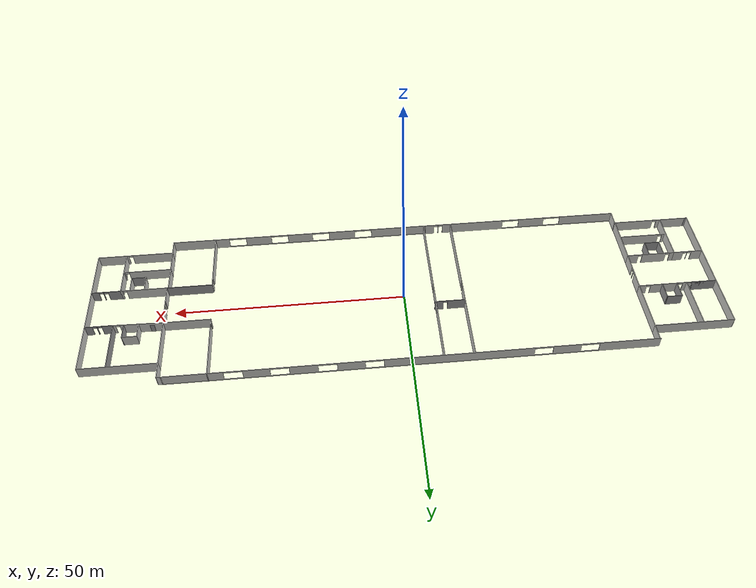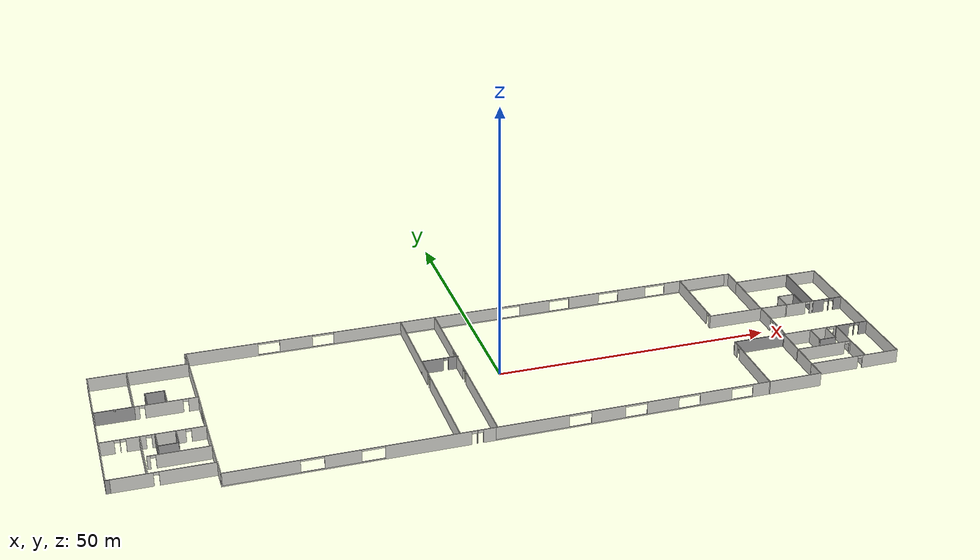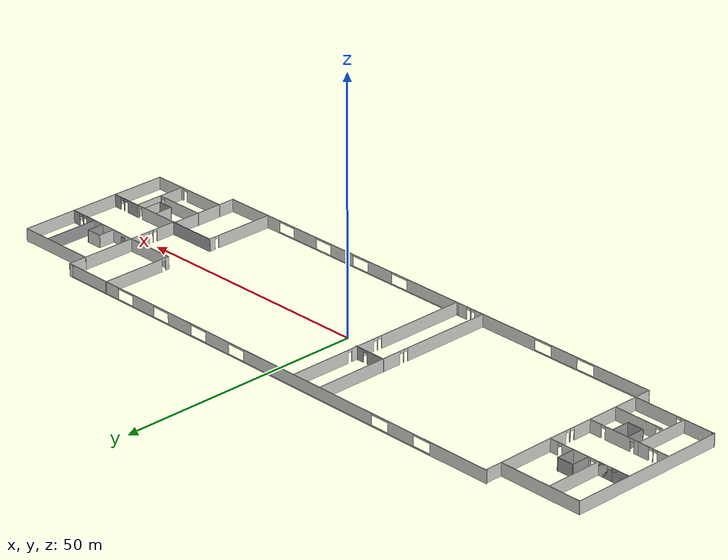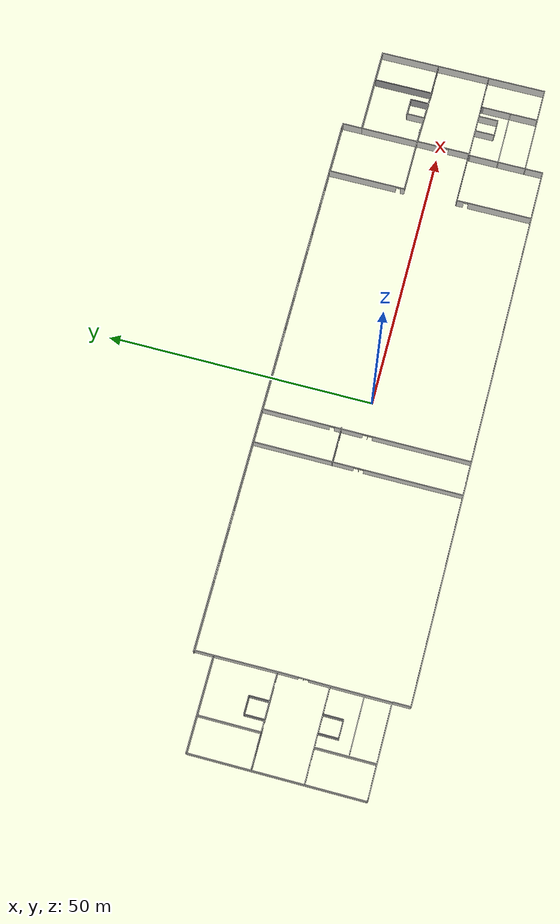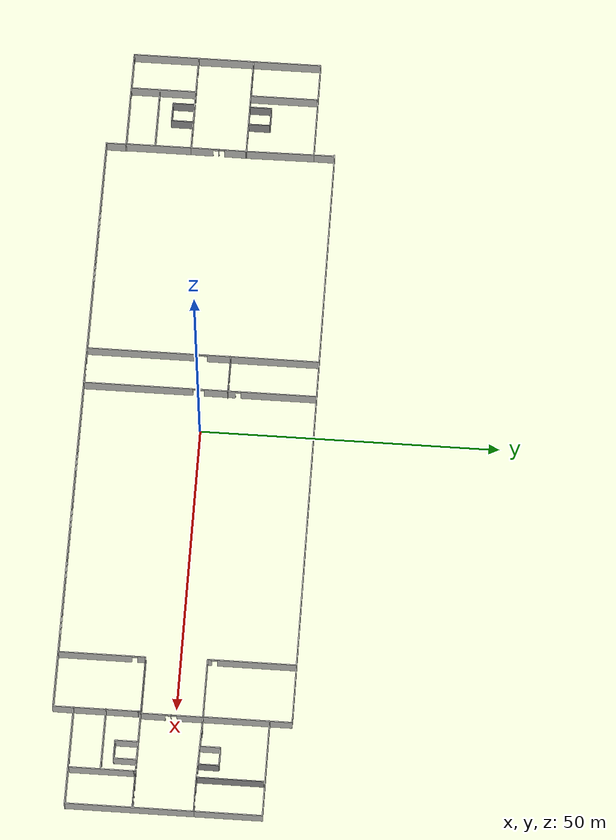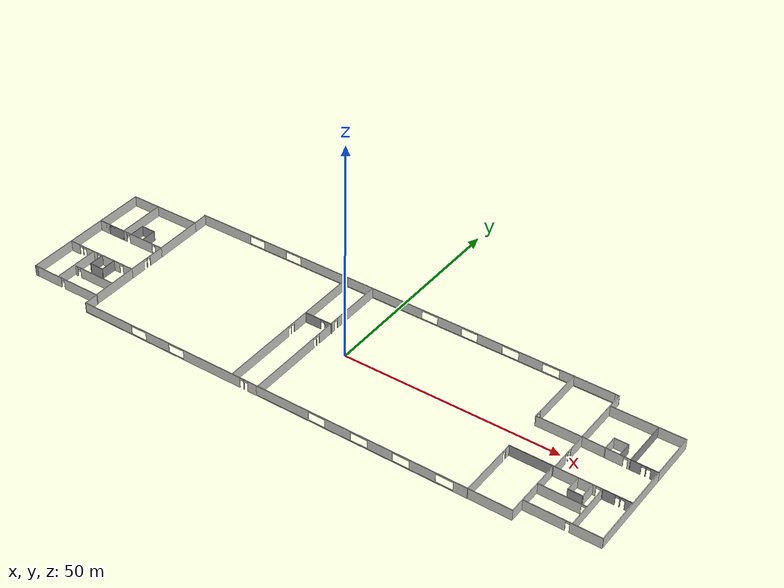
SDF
<?xml version='1.0'?>
<sdf version='1.6'>
  <model name='Erdgeschossen_labor'>
    <pose frame=''>-0.563538 -0.4802 0 0 -0 0</pose>
    <link name='Door_37'>
      <collision name='Door_37_Collision'>
        <geometry>
          <box>
            <size>0.9 0.17 2</size>
          </box>
        </geometry>
        <pose frame=''>0 0 1 0 -0 0</pose>
      </collision>
      <visual name='Door_37_Visual'>
        <pose frame=''>0 0 1 0 -0 0</pose>
        <geometry>
          <box>
            <size>0.9 0.17 2</size>
          </box>
        </geometry>
        <material>
          <script>
            <uri>file://media/materials/scripts/gazebo.material</uri>
            <name>Gazebo/Grey</name>
          </script>
        </material>
      </visual>
      <pose frame=''>54.7211 4.95557 0 0 -0 0</pose>
    </link>
    <link name='Wall_0'>
      <pose frame=''>-0.038053 19.4617 0 0 -0 0</pose>
      <visual name='Wall_0_Visual_0'>
        <pose frame=''>-45.1164 0 1.25 0 -0 0</pose>
        <geometry>
          <box>
            <size>13.0172 0.15 2.5</size>
          </box>
        </geometry>
        <material>
          <script>
            <uri>file://media/materials/scripts/gazebo.material</uri>
            <name>Gazebo/CeilingTiled</name>
          </script>
          <ambient>1 1 1 1</ambient>
        </material>
      </visual>
      <collision name='Wall_0_Collision_0'>
        <geometry>
          <box>
            <size>13.0172 0.15 2.5</size>
          </box>
        </geometry>
        <pose frame=''>-45.1164 0 1.25 0 -0 0</pose>
      </collision>
      <visual name='Wall_0_Visual_1'>
        <pose frame=''>6.50859 0 0.1 0 -0 0</pose>
        <geometry>
          <box>
            <size>90.2328 0.15 0.2</size>
          </box>
        </geometry>
        <material>
          <script>
            <uri>file://media/materials/scripts/gazebo.material</uri>
            <name>Gazebo/CeilingTiled</name>
          </script>
          <ambient>1 1 1 1</ambient>
        </material>
      </visual>
      <collision name='Wall_0_Collision_1'>
        <geometry>
          <box>
            <size>90.2328 0.15 0.2</size>
          </box>
        </geometry>
        <pose frame=''>6.50859 0 0.1 0 -0 0</pose>
      </collision>
      <visual name='Wall_0_Visual_2'>
        <pose frame=''>-31.7614 0 1.35 0 -0 0</pose>
        <geometry>
          <box>
            <size>5.93292 0.15 2.3</size>
          </box>
        </geometry>
        <material>
          <script>
            <uri>file://media/materials/scripts/gazebo.material</uri>
            <name>Gazebo/CeilingTiled</name>
          </script>
          <ambient>1 1 1 1</ambient>
        </material>
      </visual>
      <collision name='Wall_0_Collision_2'>
        <geometry>
          <box>
            <size>5.93292 0.15 2.3</size>
          </box>
        </geometry>
        <pose frame=''>-31.7614 0 1.35 0 -0 0</pose>
      </collision>
      <visual name='Wall_0_Visual_3'>
        <pose frame=''>-9.24517 0 1.35 0 -0 0</pose>
        <geometry>
          <box>
            <size>31.3395 0.15 2.3</size>
          </box>
        </geometry>
        <material>
          <script>
            <uri>file://media/materials/scripts/gazebo.material</uri>
            <name>Gazebo/CeilingTiled</name>
          </script>
          <ambient>1 1 1 1</ambient>
        </material>
      </visual>
      <collision name='Wall_0_Collision_3'>
        <geometry>
          <box>
            <size>31.3395 0.15 2.3</size>
          </box>
        </geometry>
        <pose frame=''>-9.24517 0 1.35 0 -0 0</pose>
      </collision>
      <visual name='Wall_0_Visual_4'>
        <pose frame=''>13.191 0 1.35 0 -0 0</pose>
        <geometry>
          <box>
            <size>5.77285 0.15 2.3</size>
          </box>
        </geometry>
        <material>
          <script>
            <uri>file://media/materials/scripts/gazebo.material</uri>
            <name>Gazebo/CeilingTiled</name>
          </script>
          <ambient>1 1 1 1</ambient>
        </material>
      </visual>
      <collision name='Wall_0_Collision_4'>
        <geometry>
          <box>
            <size>5.77285 0.15 2.3</size>
          </box>
        </geometry>
        <pose frame=''>13.191 0 1.35 0 -0 0</pose>
      </collision>
      <visual name='Wall_0_Visual_5'>
        <pose frame=''>22.9057 0 1.35 0 -0 0</pose>
        <geometry>
          <box>
            <size>5.89661 0.15 2.3</size>
          </box>
        </geometry>
        <material>
          <script>
            <uri>file://media/materials/scripts/gazebo.material</uri>
            <name>Gazebo/CeilingTiled</name>
          </script>
          <ambient>1 1 1 1</ambient>
        </material>
      </visual>
      <collision name='Wall_0_Collision_5'>
        <geometry>
          <box>
            <size>5.89661 0.15 2.3</size>
          </box>
        </geometry>
        <pose frame=''>22.9057 0 1.35 0 -0 0</pose>
      </collision>
      <visual name='Wall_0_Visual_6'>
        <pose frame=''>32.4967 0 1.35 0 -0 0</pose>
        <geometry>
          <box>
            <size>5.52534 0.15 2.3</size>
          </box>
        </geometry>
        <material>
          <script>
            <uri>file://media/materials/scripts/gazebo.material</uri>
            <name>Gazebo/CeilingTiled</name>
          </script>
          <ambient>1 1 1 1</ambient>
        </material>
      </visual>
      <collision name='Wall_0_Collision_6'>
        <geometry>
          <box>
            <size>5.52534 0.15 2.3</size>
          </box>
        </geometry>
        <pose frame=''>32.4967 0 1.35 0 -0 0</pose>
      </collision>
      <visual name='Wall_0_Visual_7'>
        <pose frame=''>45.3822 0 1.35 0 -0 0</pose>
        <geometry>
          <box>
            <size>12.4856 0.15 2.3</size>
          </box>
        </geometry>
        <material>
          <script>
            <uri>file://media/materials/scripts/gazebo.material</uri>
            <name>Gazebo/CeilingTiled</name>
          </script>
          <ambient>1 1 1 1</ambient>
        </material>
      </visual>
      <collision name='Wall_0_Collision_7'>
        <geometry>
          <box>
            <size>12.4856 0.15 2.3</size>
          </box>
        </geometry>
        <pose frame=''>45.3822 0 1.35 0 -0 0</pose>
      </collision>
      <visual name='Wall_0_Visual_8'>
        <pose frame=''>-36.6678 0 2.35 0 -0 0</pose>
        <geometry>
          <box>
            <size>3.88 0.15 0.3</size>
          </box>
        </geometry>
        <material>
          <script>
            <uri>file://media/materials/scripts/gazebo.material</uri>
            <name>Gazebo/CeilingTiled</name>
          </script>
          <ambient>1 1 1 1</ambient>
        </material>
      </visual>
      <collision name='Wall_0_Collision_8'>
        <geometry>
          <box>
            <size>3.88 0.15 0.3</size>
          </box>
        </geometry>
        <pose frame=''>-36.6678 0 2.35 0 -0 0</pose>
      </collision>
      <visual name='Wall_0_Visual_9'>
        <pose frame=''>-26.8549 0 2.35 0 -0 0</pose>
        <geometry>
          <box>
            <size>3.88 0.15 0.3</size>
          </box>
        </geometry>
        <material>
          <script>
            <uri>file://media/materials/scripts/gazebo.material</uri>
            <name>Gazebo/CeilingTiled</name>
          </script>
          <ambient>1 1 1 1</ambient>
        </material>
      </visual>
      <collision name='Wall_0_Collision_9'>
        <geometry>
          <box>
            <size>3.88 0.15 0.3</size>
          </box>
        </geometry>
        <pose frame=''>-26.8549 0 2.35 0 -0 0</pose>
      </collision>
      <visual name='Wall_0_Visual_10'>
        <pose frame=''>8.36458 0 2.35 0 -0 0</pose>
        <geometry>
          <box>
            <size>3.88 0.15 0.3</size>
          </box>
        </geometry>
        <material>
          <script>
            <uri>file://media/materials/scripts/gazebo.material</uri>
            <name>Gazebo/CeilingTiled</name>
          </script>
          <ambient>1 1 1 1</ambient>
        </material>
      </visual>
      <collision name='Wall_0_Collision_10'>
        <geometry>
          <box>
            <size>3.88 0.15 0.3</size>
          </box>
        </geometry>
        <pose frame=''>8.36458 0 2.35 0 -0 0</pose>
      </collision>
      <visual name='Wall_0_Visual_11'>
        <pose frame=''>18.0174 0 2.35 0 -0 0</pose>
        <geometry>
          <box>
            <size>3.88 0.15 0.3</size>
          </box>
        </geometry>
        <material>
          <script>
            <uri>file://media/materials/scripts/gazebo.material</uri>
            <name>Gazebo/CeilingTiled</name>
          </script>
          <ambient>1 1 1 1</ambient>
        </material>
      </visual>
      <collision name='Wall_0_Collision_11'>
        <geometry>
          <box>
            <size>3.88 0.15 0.3</size>
          </box>
        </geometry>
        <pose frame=''>18.0174 0 2.35 0 -0 0</pose>
      </collision>
      <visual name='Wall_0_Visual_12'>
        <pose frame=''>27.794 0 2.35 0 -0 0</pose>
        <geometry>
          <box>
            <size>3.88 0.15 0.3</size>
          </box>
        </geometry>
        <material>
          <script>
            <uri>file://media/materials/scripts/gazebo.material</uri>
            <name>Gazebo/CeilingTiled</name>
          </script>
          <ambient>1 1 1 1</ambient>
        </material>
      </visual>
      <collision name='Wall_0_Collision_12'>
        <geometry>
          <box>
            <size>3.88 0.15 0.3</size>
          </box>
        </geometry>
        <pose frame=''>27.794 0 2.35 0 -0 0</pose>
      </collision>
      <visual name='Wall_0_Visual_13'>
        <pose frame=''>37.1994 0 2.35 0 -0 0</pose>
        <geometry>
          <box>
            <size>3.88 0.15 0.3</size>
          </box>
        </geometry>
        <material>
          <script>
            <uri>file://media/materials/scripts/gazebo.material</uri>
            <name>Gazebo/CeilingTiled</name>
          </script>
          <ambient>1 1 1 1</ambient>
        </material>
      </visual>
      <collision name='Wall_0_Collision_13'>
        <geometry>
          <box>
            <size>3.88 0.15 0.3</size>
          </box>
        </geometry>
        <pose frame=''>37.1994 0 2.35 0 -0 0</pose>
      </collision>
    </link>
    <link name='Wall_10'>
      <pose frame=''>65.825 4.6812 0 0 -0 3.14159</pose>
      <visual name='Wall_10_Visual_0'>
        <pose frame=''>-2.15466 0 1.25 0 -0 0</pose>
        <geometry>
          <box>
            <size>1.69069 0.15 2.5</size>
          </box>
        </geometry>
        <material>
          <script>
            <uri>file://media/materials/scripts/gazebo.material</uri>
            <name>Gazebo/Grey</name>
          </script>
          <ambient>1 1 1 1</ambient>
        </material>
      </visual>
      <collision name='Wall_10_Collision_0'>
        <geometry>
          <box>
            <size>1.69069 0.15 2.5</size>
          </box>
        </geometry>
        <pose frame=''>-2.15466 0 1.25 0 -0 0</pose>
      </collision>
      <visual name='Wall_10_Visual_1'>
        <pose frame=''>-0.324451 0 1.25 0 -0 0</pose>
        <geometry>
          <box>
            <size>0.169725 0.15 2.5</size>
          </box>
        </geometry>
        <material>
          <script>
            <uri>file://media/materials/scripts/gazebo.material</uri>
            <name>Gazebo/Grey</name>
          </script>
          <ambient>1 1 1 1</ambient>
        </material>
      </visual>
      <collision name='Wall_10_Collision_1'>
        <geometry>
          <box>
            <size>0.169725 0.15 2.5</size>
          </box>
        </geometry>
        <pose frame=''>-0.324451 0 1.25 0 -0 0</pose>
      </collision>
      <visual name='Wall_10_Visual_2'>
        <pose frame=''>1.83021 0 1.25 0 -0 0</pose>
        <geometry>
          <box>
            <size>2.33959 0.15 2.5</size>
          </box>
        </geometry>
        <material>
          <script>
            <uri>file://media/materials/scripts/gazebo.material</uri>
            <name>Gazebo/Grey</name>
          </script>
          <ambient>1 1 1 1</ambient>
        </material>
      </visual>
      <collision name='Wall_10_Collision_2'>
        <geometry>
          <box>
            <size>2.33959 0.15 2.5</size>
          </box>
        </geometry>
        <pose frame=''>1.83021 0 1.25 0 -0 0</pose>
      </collision>
      <visual name='Wall_10_Visual_3'>
        <pose frame=''>-0.859314 0 2.25 0 -0 0</pose>
        <geometry>
          <box>
            <size>0.9 0.15 0.5</size>
          </box>
        </geometry>
        <material>
          <script>
            <uri>file://media/materials/scripts/gazebo.material</uri>
            <name>Gazebo/Grey</name>
          </script>
          <ambient>1 1 1 1</ambient>
        </material>
      </visual>
      <collision name='Wall_10_Collision_3'>
        <geometry>
          <box>
            <size>0.9 0.15 0.5</size>
          </box>
        </geometry>
        <pose frame=''>-0.859314 0 2.25 0 -0 0</pose>
      </collision>
      <visual name='Wall_10_Visual_4'>
        <pose frame=''>0.210411 0 2.25 0 -0 0</pose>
        <geometry>
          <box>
            <size>0.9 0.15 0.5</size>
          </box>
        </geometry>
        <material>
          <script>
            <uri>file://media/materials/scripts/gazebo.material</uri>
            <name>Gazebo/Grey</name>
          </script>
          <ambient>1 1 1 1</ambient>
        </material>
      </visual>
      <collision name='Wall_10_Collision_4'>
        <geometry>
          <box>
            <size>0.9 0.15 0.5</size>
          </box>
        </geometry>
        <pose frame=''>0.210411 0 2.25 0 -0 0</pose>
      </collision>
    </link>
    <link name='Wall_11'>
      <collision name='Wall_11_Collision'>
        <geometry>
          <box>
            <size>11 0.15 2.5</size>
          </box>
        </geometry>
        <pose frame=''>0 0 1.25 0 -0 0</pose>
      </collision>
      <visual name='Wall_11_Visual'>
        <pose frame=''>0 0 1.25 0 -0 0</pose>
        <geometry>
          <box>
            <size>11 0.15 2.5</size>
          </box>
        </geometry>
        <material>
          <script>
            <uri>file://media/materials/scripts/gazebo.material</uri>
            <name>Gazebo/Grey</name>
          </script>
          <ambient>1 1 1 1</ambient>
        </material>
      </visual>
      <pose frame=''>62.9 10.1062 0 0 -0 1.5708</pose>
    </link>
    <link name='Wall_13'>
      <collision name='Wall_13_Collision'>
        <geometry>
          <box>
            <size>1.04169 0.15 2.5</size>
          </box>
        </geometry>
        <pose frame=''>0 0 1.25 0 -0 0</pose>
      </collision>
      <visual name='Wall_13_Visual'>
        <pose frame=''>0 0 1.25 0 -0 0</pose>
        <geometry>
          <box>
            <size>1.04169 0.15 2.5</size>
          </box>
        </geometry>
        <material>
          <script>
            <uri>file://media/materials/scripts/gazebo.material</uri>
            <name>Gazebo/CeilingTiled</name>
          </script>
          <ambient>1 1 1 1</ambient>
        </material>
      </visual>
      <pose frame=''>51.956 19.4215 0 0 -0 3.05118</pose>
    </link>
    <link name='Wall_15'>
      <collision name='Wall_15_Collision'>
        <geometry>
          <box>
            <size>11 0.15 2.5</size>
          </box>
        </geometry>
        <pose frame=''>0 0 1.25 0 -0 0</pose>
      </collision>
      <visual name='Wall_15_Visual'>
        <pose frame=''>0 0 1.25 0 -0 0</pose>
        <geometry>
          <box>
            <size>11 0.15 2.5</size>
          </box>
        </geometry>
        <material>
          <script>
            <uri>file://media/materials/scripts/gazebo.material</uri>
            <name>Gazebo/CeilingTiled</name>
          </script>
          <ambient>1 1 1 1</ambient>
        </material>
      </visual>
      <pose frame=''>52.4 10.3562 0 0 0 -1.5708</pose>
    </link>
    <link name='Wall_16'>
      <pose frame=''>57.65 4.8062 0 0 0 -0.023805</pose>
      <visual name='Wall_16_Visual_0'>
        <pose frame=''>-0.791437 0 1.25 0 -0 0</pose>
        <geometry>
          <box>
            <size>9.0701 0.15 2.5</size>
          </box>
        </geometry>
        <material>
          <script>
            <uri>file://media/materials/scripts/gazebo.material</uri>
            <name>Gazebo/CeilingTiled</name>
          </script>
          <ambient>1 1 1 1</ambient>
        </material>
      </visual>
      <collision name='Wall_16_Collision_0'>
        <geometry>
          <box>
            <size>9.0701 0.15 2.5</size>
          </box>
        </geometry>
        <pose frame=''>-0.791437 0 1.25 0 -0 0</pose>
      </collision>
      <visual name='Wall_16_Visual_1'>
        <pose frame=''>4.98505 0 1.25 0 -0 0</pose>
        <geometry>
          <box>
            <size>0.682875 0.15 2.5</size>
          </box>
        </geometry>
        <material>
          <script>
            <uri>file://media/materials/scripts/gazebo.material</uri>
            <name>Gazebo/CeilingTiled</name>
          </script>
          <ambient>1 1 1 1</ambient>
        </material>
      </visual>
      <collision name='Wall_16_Collision_1'>
        <geometry>
          <box>
            <size>0.682875 0.15 2.5</size>
          </box>
        </geometry>
        <pose frame=''>4.98505 0 1.25 0 -0 0</pose>
      </collision>
      <visual name='Wall_16_Visual_2'>
        <pose frame=''>4.19361 0 2.25 0 -0 0</pose>
        <geometry>
          <box>
            <size>0.9 0.15 0.5</size>
          </box>
        </geometry>
        <material>
          <script>
            <uri>file://media/materials/scripts/gazebo.material</uri>
            <name>Gazebo/CeilingTiled</name>
          </script>
          <ambient>1 1 1 1</ambient>
        </material>
      </visual>
      <collision name='Wall_16_Collision_2'>
        <geometry>
          <box>
            <size>0.9 0.15 0.5</size>
          </box>
        </geometry>
        <pose frame=''>4.19361 0 2.25 0 -0 0</pose>
      </collision>
    </link>
    <link name='Wall_18'>
      <collision name='Wall_18_Collision'>
        <geometry>
          <box>
            <size>21 0.15 2.5</size>
          </box>
        </geometry>
        <pose frame=''>0 0 1.25 0 -0 0</pose>
      </collision>
      <visual name='Wall_18_Visual'>
        <pose frame=''>0 0 1.25 0 -0 0</pose>
        <geometry>
          <box>
            <size>21 0.15 2.5</size>
          </box>
        </geometry>
        <material>
          <script>
            <uri>file://media/materials/scripts/gazebo.material</uri>
            <name>Gazebo/CeilingTiled</name>
          </script>
          <ambient>1 1 1 1</ambient>
        </material>
      </visual>
      <pose frame=''>68.75 -5.7438 0 0 0 -1.5708</pose>
    </link>
    <link name='Wall_19'>
      <pose frame=''>60.45 -16.1688 0 0 -0 3.14159</pose>
      <visual name='Wall_19_Visual_0'>
        <pose frame=''>-4.96727 0 1.25 0 -0 0</pose>
        <geometry>
          <box>
            <size>6.81547 0.15 2.5</size>
          </box>
        </geometry>
        <material>
          <script>
            <uri>file://media/materials/scripts/gazebo.material</uri>
            <name>Gazebo/CeilingTiled</name>
          </script>
          <ambient>1 1 1 1</ambient>
        </material>
      </visual>
      <collision name='Wall_19_Collision_0'>
        <geometry>
          <box>
            <size>6.81547 0.15 2.5</size>
          </box>
        </geometry>
        <pose frame=''>-4.96727 0 1.25 0 -0 0</pose>
      </collision>
      <visual name='Wall_19_Visual_1'>
        <pose frame=''>3.85773 0 1.25 0 -0 0</pose>
        <geometry>
          <box>
            <size>9.03453 0.15 2.5</size>
          </box>
        </geometry>
        <material>
          <script>
            <uri>file://media/materials/scripts/gazebo.material</uri>
            <name>Gazebo/CeilingTiled</name>
          </script>
          <ambient>1 1 1 1</ambient>
        </material>
      </visual>
      <collision name='Wall_19_Collision_1'>
        <geometry>
          <box>
            <size>9.03453 0.15 2.5</size>
          </box>
        </geometry>
        <pose frame=''>3.85773 0 1.25 0 -0 0</pose>
      </collision>
      <visual name='Wall_19_Visual_2'>
        <pose frame=''>-1.10953 0 2.25 0 -0 0</pose>
        <geometry>
          <box>
            <size>0.9 0.15 0.5</size>
          </box>
        </geometry>
        <material>
          <script>
            <uri>file://media/materials/scripts/gazebo.material</uri>
            <name>Gazebo/CeilingTiled</name>
          </script>
          <ambient>1 1 1 1</ambient>
        </material>
      </visual>
      <collision name='Wall_19_Collision_2'>
        <geometry>
          <box>
            <size>0.9 0.15 0.5</size>
          </box>
        </geometry>
        <pose frame=''>-1.10953 0 2.25 0 -0 0</pose>
      </collision>
    </link>
    <link name='Wall_20'>
      <collision name='Wall_20_Collision'>
        <geometry>
          <box>
            <size>10.75 0.15 2.5</size>
          </box>
        </geometry>
        <pose frame=''>0 0 1.25 0 -0 0</pose>
      </collision>
      <visual name='Wall_20_Visual'>
        <pose frame=''>0 0 1.25 0 -0 0</pose>
        <geometry>
          <box>
            <size>10.75 0.15 2.5</size>
          </box>
        </geometry>
        <material>
          <script>
            <uri>file://media/materials/scripts/gazebo.material</uri>
            <name>Gazebo/CeilingTiled</name>
          </script>
          <ambient>1 1 1 1</ambient>
        </material>
      </visual>
      <pose frame=''>52.15 -10.8688 0 0 -0 1.5708</pose>
    </link>
    <link name='Wall_22'>
      <collision name='Wall_22_Collision'>
        <geometry>
          <box>
            <size>10.5 0.15 2.5</size>
          </box>
        </geometry>
        <pose frame=''>0 0 1.25 0 -0 0</pose>
      </collision>
      <visual name='Wall_22_Visual'>
        <pose frame=''>0 0 1.25 0 -0 0</pose>
        <geometry>
          <box>
            <size>10.5 0.15 2.5</size>
          </box>
        </geometry>
        <material>
          <script>
            <uri>file://media/materials/scripts/gazebo.material</uri>
            <name>Gazebo/CeilingTiled</name>
          </script>
          <ambient>1 1 1 1</ambient>
        </material>
      </visual>
      <pose frame=''>62.5 -10.7438 0 0 0 -1.5708</pose>
    </link>
    <link name='Wall_25'>
      <collision name='Wall_25_Collision'>
        <geometry>
          <box>
            <size>0.5 0.15 2.5</size>
          </box>
        </geometry>
        <pose frame=''>0 0 1.25 0 -0 0</pose>
      </collision>
      <visual name='Wall_25_Visual'>
        <pose frame=''>0 0 1.25 0 -0 0</pose>
        <geometry>
          <box>
            <size>0.5 0.15 2.5</size>
          </box>
        </geometry>
        <material>
          <script>
            <uri>file://media/materials/scripts/gazebo.material</uri>
            <name>Gazebo/Grey</name>
          </script>
          <ambient>1 1 1 1</ambient>
        </material>
      </visual>
      <pose frame=''>52.15 -5.3938 0 0 -0 1.5708</pose>
    </link>
    <link name='Wall_26'>
      <pose frame=''>57.325 -5.2188 0 0 -0 0</pose>
      <visual name='Wall_26_Visual_0'>
        <pose frame=''>-0.710538 0 1.25 0 -0 0</pose>
        <geometry>
          <box>
            <size>9.07892 0.15 2.5</size>
          </box>
        </geometry>
        <material>
          <script>
            <uri>file://media/materials/scripts/gazebo.material</uri>
            <name>Gazebo/CeilingTiled</name>
          </script>
          <ambient>1 1 1 1</ambient>
        </material>
      </visual>
      <collision name='Wall_26_Collision_0'>
        <geometry>
          <box>
            <size>9.07892 0.15 2.5</size>
          </box>
        </geometry>
        <pose frame=''>-0.710538 0 1.25 0 -0 0</pose>
      </collision>
      <visual name='Wall_26_Visual_1'>
        <pose frame=''>4.98946 0 1.25 0 -0 0</pose>
        <geometry>
          <box>
            <size>0.521077 0.15 2.5</size>
          </box>
        </geometry>
        <material>
          <script>
            <uri>file://media/materials/scripts/gazebo.material</uri>
            <name>Gazebo/CeilingTiled</name>
          </script>
          <ambient>1 1 1 1</ambient>
        </material>
      </visual>
      <collision name='Wall_26_Collision_1'>
        <geometry>
          <box>
            <size>0.521077 0.15 2.5</size>
          </box>
        </geometry>
        <pose frame=''>4.98946 0 1.25 0 -0 0</pose>
      </collision>
      <visual name='Wall_26_Visual_2'>
        <pose frame=''>4.27892 0 2.25 0 -0 0</pose>
        <geometry>
          <box>
            <size>0.9 0.15 0.5</size>
          </box>
        </geometry>
        <material>
          <script>
            <uri>file://media/materials/scripts/gazebo.material</uri>
            <name>Gazebo/CeilingTiled</name>
          </script>
          <ambient>1 1 1 1</ambient>
        </material>
      </visual>
      <collision name='Wall_26_Collision_2'>
        <geometry>
          <box>
            <size>0.9 0.15 0.5</size>
          </box>
        </geometry>
        <pose frame=''>4.27892 0 2.25 0 -0 0</pose>
      </collision>
    </link>
    <link name='Wall_27'>
      <collision name='Wall_27_Collision'>
        <geometry>
          <box>
            <size>0.5 0.15 2.5</size>
          </box>
        </geometry>
        <pose frame=''>0 0 1.25 0 -0 0</pose>
      </collision>
      <visual name='Wall_27_Visual'>
        <pose frame=''>0 0 1.25 0 -0 0</pose>
        <geometry>
          <box>
            <size>0.5 0.15 2.5</size>
          </box>
        </geometry>
        <material>
          <script>
            <uri>file://media/materials/scripts/gazebo.material</uri>
            <name>Gazebo/Grey</name>
          </script>
          <ambient>1 1 1 1</ambient>
        </material>
      </visual>
      <pose frame=''>62.5 -5.3938 0 0 0 -1.5708</pose>
    </link>
    <link name='Wall_29'>
      <pose frame=''>65.55 -5.2188 0 0 -0 0</pose>
      <visual name='Wall_29_Visual_0'>
        <pose frame=''>-1.74988 0 1.25 0 -0 0</pose>
        <geometry>
          <box>
            <size>2.75023 0.15 2.5</size>
          </box>
        </geometry>
        <material>
          <script>
            <uri>file://media/materials/scripts/gazebo.material</uri>
            <name>Gazebo/Grey</name>
          </script>
          <ambient>1 1 1 1</ambient>
        </material>
      </visual>
      <collision name='Wall_29_Collision_0'>
        <geometry>
          <box>
            <size>2.75023 0.15 2.5</size>
          </box>
        </geometry>
        <pose frame=''>-1.74988 0 1.25 0 -0 0</pose>
      </collision>
      <visual name='Wall_29_Visual_1'>
        <pose frame=''>0.607143 0 1.25 0 -0 0</pose>
        <geometry>
          <box>
            <size>0.16382 0.15 2.5</size>
          </box>
        </geometry>
        <material>
          <script>
            <uri>file://media/materials/scripts/gazebo.material</uri>
            <name>Gazebo/Grey</name>
          </script>
          <ambient>1 1 1 1</ambient>
        </material>
      </visual>
      <collision name='Wall_29_Collision_1'>
        <geometry>
          <box>
            <size>0.16382 0.15 2.5</size>
          </box>
        </geometry>
        <pose frame=''>0.607143 0 1.25 0 -0 0</pose>
      </collision>
      <visual name='Wall_29_Visual_2'>
        <pose frame=''>2.35703 0 1.25 0 -0 0</pose>
        <geometry>
          <box>
            <size>1.53595 0.15 2.5</size>
          </box>
        </geometry>
        <material>
          <script>
            <uri>file://media/materials/scripts/gazebo.material</uri>
            <name>Gazebo/Grey</name>
          </script>
          <ambient>1 1 1 1</ambient>
        </material>
      </visual>
      <collision name='Wall_29_Collision_2'>
        <geometry>
          <box>
            <size>1.53595 0.15 2.5</size>
          </box>
        </geometry>
        <pose frame=''>2.35703 0 1.25 0 -0 0</pose>
      </collision>
      <visual name='Wall_29_Visual_3'>
        <pose frame=''>0.075233 0 2.25 0 -0 0</pose>
        <geometry>
          <box>
            <size>0.9 0.15 0.5</size>
          </box>
        </geometry>
        <material>
          <script>
            <uri>file://media/materials/scripts/gazebo.material</uri>
            <name>Gazebo/Grey</name>
          </script>
          <ambient>1 1 1 1</ambient>
        </material>
      </visual>
      <collision name='Wall_29_Collision_3'>
        <geometry>
          <box>
            <size>0.9 0.15 0.5</size>
          </box>
        </geometry>
        <pose frame=''>0.075233 0 2.25 0 -0 0</pose>
      </collision>
      <visual name='Wall_29_Visual_4'>
        <pose frame=''>1.13905 0 2.25 0 -0 0</pose>
        <geometry>
          <box>
            <size>0.9 0.15 0.5</size>
          </box>
        </geometry>
        <material>
          <script>
            <uri>file://media/materials/scripts/gazebo.material</uri>
            <name>Gazebo/Grey</name>
          </script>
          <ambient>1 1 1 1</ambient>
        </material>
      </visual>
      <collision name='Wall_29_Collision_4'>
        <geometry>
          <box>
            <size>0.9 0.15 0.5</size>
          </box>
        </geometry>
        <pose frame=''>1.13905 0 2.25 0 -0 0</pose>
      </collision>
    </link>
    <link name='Wall_31'>
      <collision name='Wall_31_Collision'>
        <geometry>
          <box>
            <size>3.5 0.15 2.5</size>
          </box>
        </geometry>
        <pose frame=''>0 0 1.25 0 -0 0</pose>
      </collision>
      <visual name='Wall_31_Visual'>
        <pose frame=''>0 0 1.25 0 -0 0</pose>
        <geometry>
          <box>
            <size>3.5 0.15 2.5</size>
          </box>
        </geometry>
        <material>
          <script>
            <uri>file://media/materials/scripts/gazebo.material</uri>
            <name>Gazebo/CeilingTiled</name>
          </script>
          <ambient>1 1 1 1</ambient>
        </material>
      </visual>
      <pose frame=''>52.15 -17.8438 0 0 0 -1.5708</pose>
    </link>
    <link name='Wall_32'>
      <pose frame=''>22.85 -19.5188 0 0 -0 3.14159</pose>
      <visual name='Wall_32_Visual_0'>
        <pose frame=''>-22.984 0 1.25 0 -0 0</pose>
        <geometry>
          <box>
            <size>12.7819 0.15 2.5</size>
          </box>
        </geometry>
        <material>
          <script>
            <uri>file://media/materials/scripts/gazebo.material</uri>
            <name>Gazebo/CeilingTiled</name>
          </script>
          <ambient>1 1 1 1</ambient>
        </material>
      </visual>
      <collision name='Wall_32_Collision_0'>
        <geometry>
          <box>
            <size>12.7819 0.15 2.5</size>
          </box>
        </geometry>
        <pose frame=''>-22.984 0 1.25 0 -0 0</pose>
      </collision>
      <visual name='Wall_32_Visual_1'>
        <pose frame=''>6.39096 0 0.1 0 -0 0</pose>
        <geometry>
          <box>
            <size>45.9681 0.15 0.2</size>
          </box>
        </geometry>
        <material>
          <script>
            <uri>file://media/materials/scripts/gazebo.material</uri>
            <name>Gazebo/CeilingTiled</name>
          </script>
          <ambient>1 1 1 1</ambient>
        </material>
      </visual>
      <collision name='Wall_32_Collision_1'>
        <geometry>
          <box>
            <size>45.9681 0.15 0.2</size>
          </box>
        </geometry>
        <pose frame=''>6.39096 0 0.1 0 -0 0</pose>
      </collision>
      <visual name='Wall_32_Visual_2'>
        <pose frame=''>-9.79822 0 1.35 0 -0 0</pose>
        <geometry>
          <box>
            <size>5.82974 0.15 2.3</size>
          </box>
        </geometry>
        <material>
          <script>
            <uri>file://media/materials/scripts/gazebo.material</uri>
            <name>Gazebo/CeilingTiled</name>
          </script>
          <ambient>1 1 1 1</ambient>
        </material>
      </visual>
      <collision name='Wall_32_Collision_2'>
        <geometry>
          <box>
            <size>5.82974 0.15 2.3</size>
          </box>
        </geometry>
        <pose frame=''>-9.79822 0 1.35 0 -0 0</pose>
      </collision>
      <visual name='Wall_32_Visual_3'>
        <pose frame=''>-0.149557 0 1.35 0 -0 0</pose>
        <geometry>
          <box>
            <size>5.70758 0.15 2.3</size>
          </box>
        </geometry>
        <material>
          <script>
            <uri>file://media/materials/scripts/gazebo.material</uri>
            <name>Gazebo/CeilingTiled</name>
          </script>
          <ambient>1 1 1 1</ambient>
        </material>
      </visual>
      <collision name='Wall_32_Collision_3'>
        <geometry>
          <box>
            <size>5.70758 0.15 2.3</size>
          </box>
        </geometry>
        <pose frame=''>-0.149557 0 1.35 0 -0 0</pose>
      </collision>
      <visual name='Wall_32_Visual_4'>
        <pose frame=''>9.60231 0 1.35 0 -0 0</pose>
        <geometry>
          <box>
            <size>6.03615 0.15 2.3</size>
          </box>
        </geometry>
        <material>
          <script>
            <uri>file://media/materials/scripts/gazebo.material</uri>
            <name>Gazebo/CeilingTiled</name>
          </script>
          <ambient>1 1 1 1</ambient>
        </material>
      </visual>
      <collision name='Wall_32_Collision_4'>
        <geometry>
          <box>
            <size>6.03615 0.15 2.3</size>
          </box>
        </geometry>
        <pose frame=''>9.60231 0 1.35 0 -0 0</pose>
      </collision>
      <visual name='Wall_32_Visual_5'>
        <pose frame=''>22.9377 0 1.35 0 -0 0</pose>
        <geometry>
          <box>
            <size>12.8746 0.15 2.3</size>
          </box>
        </geometry>
        <material>
          <script>
            <uri>file://media/materials/scripts/gazebo.material</uri>
            <name>Gazebo/CeilingTiled</name>
          </script>
          <ambient>1 1 1 1</ambient>
        </material>
      </visual>
      <collision name='Wall_32_Collision_5'>
        <geometry>
          <box>
            <size>12.8746 0.15 2.3</size>
          </box>
        </geometry>
        <pose frame=''>22.9377 0 1.35 0 -0 0</pose>
      </collision>
      <visual name='Wall_32_Visual_6'>
        <pose frame=''>-14.6531 0 2.35 0 -0 0</pose>
        <geometry>
          <box>
            <size>3.88 0.15 0.3</size>
          </box>
        </geometry>
        <material>
          <script>
            <uri>file://media/materials/scripts/gazebo.material</uri>
            <name>Gazebo/CeilingTiled</name>
          </script>
          <ambient>1 1 1 1</ambient>
        </material>
      </visual>
      <collision name='Wall_32_Collision_6'>
        <geometry>
          <box>
            <size>3.88 0.15 0.3</size>
          </box>
        </geometry>
        <pose frame=''>-14.6531 0 2.35 0 -0 0</pose>
      </collision>
      <visual name='Wall_32_Visual_7'>
        <pose frame=''>-4.94335 0 2.35 0 -0 0</pose>
        <geometry>
          <box>
            <size>3.88 0.15 0.3</size>
          </box>
        </geometry>
        <material>
          <script>
            <uri>file://media/materials/scripts/gazebo.material</uri>
            <name>Gazebo/CeilingTiled</name>
          </script>
          <ambient>1 1 1 1</ambient>
        </material>
      </visual>
      <collision name='Wall_32_Collision_7'>
        <geometry>
          <box>
            <size>3.88 0.15 0.3</size>
          </box>
        </geometry>
        <pose frame=''>-4.94335 0 2.35 0 -0 0</pose>
      </collision>
      <visual name='Wall_32_Visual_8'>
        <pose frame=''>4.64423 0 2.35 0 -0 0</pose>
        <geometry>
          <box>
            <size>3.88 0.15 0.3</size>
          </box>
        </geometry>
        <material>
          <script>
            <uri>file://media/materials/scripts/gazebo.material</uri>
            <name>Gazebo/CeilingTiled</name>
          </script>
          <ambient>1 1 1 1</ambient>
        </material>
      </visual>
      <collision name='Wall_32_Collision_8'>
        <geometry>
          <box>
            <size>3.88 0.15 0.3</size>
          </box>
        </geometry>
        <pose frame=''>4.64423 0 2.35 0 -0 0</pose>
      </collision>
      <visual name='Wall_32_Visual_9'>
        <pose frame=''>14.5604 0 2.35 0 -0 0</pose>
        <geometry>
          <box>
            <size>3.88 0.15 0.3</size>
          </box>
        </geometry>
        <material>
          <script>
            <uri>file://media/materials/scripts/gazebo.material</uri>
            <name>Gazebo/CeilingTiled</name>
          </script>
          <ambient>1 1 1 1</ambient>
        </material>
      </visual>
      <collision name='Wall_32_Collision_9'>
        <geometry>
          <box>
            <size>3.88 0.15 0.3</size>
          </box>
        </geometry>
        <pose frame=''>14.5604 0 2.35 0 -0 0</pose>
      </collision>
    </link>
    <link name='Wall_34'>
      <pose frame=''>-28.875 -19.5188 0 0 -0 3.14159</pose>
      <visual name='Wall_34_Visual_0'>
        <pose frame=''>-21.4228 0 1.25 0 -0 0</pose>
        <geometry>
          <box>
            <size>2.1544 0.15 2.5</size>
          </box>
        </geometry>
        <material>
          <script>
            <uri>file://media/materials/scripts/gazebo.material</uri>
            <name>Gazebo/CeilingTiled</name>
          </script>
          <ambient>1 1 1 1</ambient>
        </material>
      </visual>
      <collision name='Wall_34_Collision_0'>
        <geometry>
          <box>
            <size>2.1544 0.15 2.5</size>
          </box>
        </geometry>
        <pose frame=''>-21.4228 0 1.25 0 -0 0</pose>
      </collision>
      <visual name='Wall_34_Visual_1'>
        <pose frame=''>-19.364 0 1.25 0 -0 0</pose>
        <geometry>
          <box>
            <size>0.163249 0.15 2.5</size>
          </box>
        </geometry>
        <material>
          <script>
            <uri>file://media/materials/scripts/gazebo.material</uri>
            <name>Gazebo/CeilingTiled</name>
          </script>
          <ambient>1 1 1 1</ambient>
        </material>
      </visual>
      <collision name='Wall_34_Collision_1'>
        <geometry>
          <box>
            <size>0.163249 0.15 2.5</size>
          </box>
        </geometry>
        <pose frame=''>-19.364 0 1.25 0 -0 0</pose>
      </collision>
      <visual name='Wall_34_Visual_2'>
        <pose frame=''>-11.1612 0 1.25 0 -0 0</pose>
        <geometry>
          <box>
            <size>14.4423 0.15 2.5</size>
          </box>
        </geometry>
        <material>
          <script>
            <uri>file://media/materials/scripts/gazebo.material</uri>
            <name>Gazebo/CeilingTiled</name>
          </script>
          <ambient>1 1 1 1</ambient>
        </material>
      </visual>
      <collision name='Wall_34_Collision_2'>
        <geometry>
          <box>
            <size>14.4423 0.15 2.5</size>
          </box>
        </geometry>
        <pose frame=''>-11.1612 0 1.25 0 -0 0</pose>
      </collision>
      <visual name='Wall_34_Visual_3'>
        <pose frame=''>9.27999 0 0.1 0 -0 0</pose>
        <geometry>
          <box>
            <size>26.44 0.15 0.2</size>
          </box>
        </geometry>
        <material>
          <script>
            <uri>file://media/materials/scripts/gazebo.material</uri>
            <name>Gazebo/CeilingTiled</name>
          </script>
          <ambient>1 1 1 1</ambient>
        </material>
      </visual>
      <collision name='Wall_34_Collision_3'>
        <geometry>
          <box>
            <size>26.44 0.15 0.2</size>
          </box>
        </geometry>
        <pose frame=''>9.27999 0 0.1 0 -0 0</pose>
      </collision>
      <visual name='Wall_34_Visual_4'>
        <pose frame=''>2.95951 0 1.35 0 -0 0</pose>
        <geometry>
          <box>
            <size>6.03908 0.15 2.3</size>
          </box>
        </geometry>
        <material>
          <script>
            <uri>file://media/materials/scripts/gazebo.material</uri>
            <name>Gazebo/CeilingTiled</name>
          </script>
          <ambient>1 1 1 1</ambient>
        </material>
      </visual>
      <collision name='Wall_34_Collision_4'>
        <geometry>
          <box>
            <size>6.03908 0.15 2.3</size>
          </box>
        </geometry>
        <pose frame=''>2.95951 0 1.35 0 -0 0</pose>
      </collision>
      <visual name='Wall_34_Visual_5'>
        <pose frame=''>16.1795 0 1.35 0 -0 0</pose>
        <geometry>
          <box>
            <size>12.641 0.15 2.3</size>
          </box>
        </geometry>
        <material>
          <script>
            <uri>file://media/materials/scripts/gazebo.material</uri>
            <name>Gazebo/CeilingTiled</name>
          </script>
          <ambient>1 1 1 1</ambient>
        </material>
      </visual>
      <collision name='Wall_34_Collision_5'>
        <geometry>
          <box>
            <size>12.641 0.15 2.3</size>
          </box>
        </geometry>
        <pose frame=''>16.1795 0 1.35 0 -0 0</pose>
      </collision>
      <visual name='Wall_34_Visual_6'>
        <pose frame=''>-19.8956 0 2.25 0 -0 0</pose>
        <geometry>
          <box>
            <size>0.9 0.15 0.5</size>
          </box>
        </geometry>
        <material>
          <script>
            <uri>file://media/materials/scripts/gazebo.material</uri>
            <name>Gazebo/CeilingTiled</name>
          </script>
          <ambient>1 1 1 1</ambient>
        </material>
      </visual>
      <collision name='Wall_34_Collision_6'>
        <geometry>
          <box>
            <size>0.9 0.15 0.5</size>
          </box>
        </geometry>
        <pose frame=''>-19.8956 0 2.25 0 -0 0</pose>
      </collision>
      <visual name='Wall_34_Visual_7'>
        <pose frame=''>-18.8323 0 2.25 0 -0 0</pose>
        <geometry>
          <box>
            <size>0.9 0.15 0.5</size>
          </box>
        </geometry>
        <material>
          <script>
            <uri>file://media/materials/scripts/gazebo.material</uri>
            <name>Gazebo/CeilingTiled</name>
          </script>
          <ambient>1 1 1 1</ambient>
        </material>
      </visual>
      <collision name='Wall_34_Collision_7'>
        <geometry>
          <box>
            <size>0.9 0.15 0.5</size>
          </box>
        </geometry>
        <pose frame=''>-18.8323 0 2.25 0 -0 0</pose>
      </collision>
      <visual name='Wall_34_Visual_8'>
        <pose frame=''>-2.00003 0 2.35 0 -0 0</pose>
        <geometry>
          <box>
            <size>3.88 0.15 0.3</size>
          </box>
        </geometry>
        <material>
          <script>
            <uri>file://media/materials/scripts/gazebo.material</uri>
            <name>Gazebo/CeilingTiled</name>
          </script>
          <ambient>1 1 1 1</ambient>
        </material>
      </visual>
      <collision name='Wall_34_Collision_8'>
        <geometry>
          <box>
            <size>3.88 0.15 0.3</size>
          </box>
        </geometry>
        <pose frame=''>-2.00003 0 2.35 0 -0 0</pose>
      </collision>
      <visual name='Wall_34_Visual_9'>
        <pose frame=''>7.91905 0 2.35 0 -0 0</pose>
        <geometry>
          <box>
            <size>3.88 0.15 0.3</size>
          </box>
        </geometry>
        <material>
          <script>
            <uri>file://media/materials/scripts/gazebo.material</uri>
            <name>Gazebo/CeilingTiled</name>
          </script>
          <ambient>1 1 1 1</ambient>
        </material>
      </visual>
      <collision name='Wall_34_Collision_9'>
        <geometry>
          <box>
            <size>3.88 0.15 0.3</size>
          </box>
        </geometry>
        <pose frame=''>7.91905 0 2.35 0 -0 0</pose>
      </collision>
    </link>
    <link name='Wall_35'>
      <collision name='Wall_35_Collision'>
        <geometry>
          <box>
            <size>3.5 0.15 2.5</size>
          </box>
        </geometry>
        <pose frame=''>0 0 1.25 0 -0 0</pose>
      </collision>
      <visual name='Wall_35_Visual'>
        <pose frame=''>0 0 1.25 0 -0 0</pose>
        <geometry>
          <box>
            <size>3.5 0.15 2.5</size>
          </box>
        </geometry>
        <material>
          <script>
            <uri>file://media/materials/scripts/gazebo.material</uri>
            <name>Gazebo/CeilingTiled</name>
          </script>
          <ambient>1 1 1 1</ambient>
        </material>
      </visual>
      <pose frame=''>-51.3 -17.8438 0 0 -0 1.5708</pose>
    </link>
    <link name='Wall_36'>
      <pose frame=''>-59.725 -16.1688 0 0 -0 3.14159</pose>
      <visual name='Wall_36_Visual_0'>
        <pose frame=''>-3.88185 0 1.25 0 -0 0</pose>
        <geometry>
          <box>
            <size>9.23631 0.15 2.5</size>
          </box>
        </geometry>
        <material>
          <script>
            <uri>file://media/materials/scripts/gazebo.material</uri>
            <name>Gazebo/CeilingTiled</name>
          </script>
          <ambient>1 1 1 1</ambient>
        </material>
      </visual>
      <collision name='Wall_36_Collision_0'>
        <geometry>
          <box>
            <size>9.23631 0.15 2.5</size>
          </box>
        </geometry>
        <pose frame=''>-3.88185 0 1.25 0 -0 0</pose>
      </collision>
      <visual name='Wall_36_Visual_1'>
        <pose frame=''>5.06815 0 1.25 0 -0 0</pose>
        <geometry>
          <box>
            <size>6.86369 0.15 2.5</size>
          </box>
        </geometry>
        <material>
          <script>
            <uri>file://media/materials/scripts/gazebo.material</uri>
            <name>Gazebo/CeilingTiled</name>
          </script>
          <ambient>1 1 1 1</ambient>
        </material>
      </visual>
      <collision name='Wall_36_Collision_1'>
        <geometry>
          <box>
            <size>6.86369 0.15 2.5</size>
          </box>
        </geometry>
        <pose frame=''>5.06815 0 1.25 0 -0 0</pose>
      </collision>
      <visual name='Wall_36_Visual_2'>
        <pose frame=''>1.18631 0 2.25 0 -0 0</pose>
        <geometry>
          <box>
            <size>0.9 0.15 0.5</size>
          </box>
        </geometry>
        <material>
          <script>
            <uri>file://media/materials/scripts/gazebo.material</uri>
            <name>Gazebo/CeilingTiled</name>
          </script>
          <ambient>1 1 1 1</ambient>
        </material>
      </visual>
      <collision name='Wall_36_Collision_2'>
        <geometry>
          <box>
            <size>0.9 0.15 0.5</size>
          </box>
        </geometry>
        <pose frame=''>1.18631 0 2.25 0 -0 0</pose>
      </collision>
    </link>
    <link name='Wall_38'>
      <collision name='Wall_38_Collision'>
        <geometry>
          <box>
            <size>0.75 0.15 2.5</size>
          </box>
        </geometry>
        <pose frame=''>0 0 1.25 0 -0 0</pose>
      </collision>
      <visual name='Wall_38_Visual'>
        <pose frame=''>0 0 1.25 0 -0 0</pose>
        <geometry>
          <box>
            <size>0.75 0.15 2.5</size>
          </box>
        </geometry>
        <material>
          <script>
            <uri>file://media/materials/scripts/gazebo.material</uri>
            <name>Gazebo/Grey</name>
          </script>
          <ambient>1 1 1 1</ambient>
        </material>
      </visual>
      <pose frame=''>-68.45 -16.1688 0 0 -0 3.14159</pose>
    </link>
    <link name='Wall_39'>
      <collision name='Wall_39_Collision'>
        <geometry>
          <box>
            <size>32.25 0.15 2.5</size>
          </box>
        </geometry>
        <pose frame=''>0 0 1.25 0 -0 0</pose>
      </collision>
      <visual name='Wall_39_Visual'>
        <pose frame=''>0 0 1.25 0 -0 0</pose>
        <geometry>
          <box>
            <size>32.25 0.15 2.5</size>
          </box>
        </geometry>
        <material>
          <script>
            <uri>file://media/materials/scripts/gazebo.material</uri>
            <name>Gazebo/CeilingTiled</name>
          </script>
          <ambient>1 1 1 1</ambient>
        </material>
      </visual>
      <pose frame=''>-68.75 -0.118799 0 0 -0 1.5708</pose>
    </link>
    <link name='Wall_40'>
      <collision name='Wall_40_Collision'>
        <geometry>
          <box>
            <size>17.5 0.15 2.5</size>
          </box>
        </geometry>
        <pose frame=''>0 0 1.25 0 -0 0</pose>
      </collision>
      <visual name='Wall_40_Visual'>
        <pose frame=''>0 0 1.25 0 -0 0</pose>
        <geometry>
          <box>
            <size>17.5 0.15 2.5</size>
          </box>
        </geometry>
        <material>
          <script>
            <uri>file://media/materials/scripts/gazebo.material</uri>
            <name>Gazebo/CeilingTiled</name>
          </script>
          <ambient>1 1 1 1</ambient>
        </material>
      </visual>
      <pose frame=''>-60.075 15.9312 0 0 -0 0</pose>
    </link>
    <link name='Wall_41'>
      <collision name='Wall_41_Collision'>
        <geometry>
          <box>
            <size>3.5 0.15 2.5</size>
          </box>
        </geometry>
        <pose frame=''>0 0 1.25 0 -0 0</pose>
      </collision>
      <visual name='Wall_41_Visual'>
        <pose frame=''>0 0 1.25 0 -0 0</pose>
        <geometry>
          <box>
            <size>3.5 0.15 2.5</size>
          </box>
        </geometry>
        <material>
          <script>
            <uri>file://media/materials/scripts/gazebo.material</uri>
            <name>Gazebo/CeilingTiled</name>
          </script>
          <ambient>1 1 1 1</ambient>
        </material>
      </visual>
      <pose frame=''>-51.4 17.6062 0 0 -0 1.5708</pose>
    </link>
    <link name='Wall_43'>
      <collision name='Wall_43_Collision'>
        <geometry>
          <box>
            <size>11.5 0.15 2.5</size>
          </box>
        </geometry>
        <pose frame=''>0 0 1.25 0 -0 0</pose>
      </collision>
      <visual name='Wall_43_Visual'>
        <pose frame=''>0 0 1.25 0 -0 0</pose>
        <geometry>
          <box>
            <size>11.5 0.15 2.5</size>
          </box>
        </geometry>
        <material>
          <script>
            <uri>file://media/materials/scripts/gazebo.material</uri>
            <name>Gazebo/CeilingTiled</name>
          </script>
          <ambient>1 1 1 1</ambient>
        </material>
      </visual>
      <pose frame=''>-62.0601 10.0639 0 0 0 -1.5708</pose>
    </link>
    <link name='Wall_44'>
      <collision name='Wall_44_Collision'>
        <geometry>
          <box>
            <size>6.75 0.15 2.5</size>
          </box>
        </geometry>
        <pose frame=''>0 0 1.25 0 -0 0</pose>
      </collision>
      <visual name='Wall_44_Visual'>
        <pose frame=''>0 0 1.25 0 -0 0</pose>
        <geometry>
          <box>
            <size>6.75 0.15 2.5</size>
          </box>
        </geometry>
        <material>
          <script>
            <uri>file://media/materials/scripts/gazebo.material</uri>
            <name>Gazebo/Grey</name>
          </script>
          <ambient>1 1 1 1</ambient>
        </material>
      </visual>
      <pose frame=''>-65.3601 4.3889 0 0 -0 3.14159</pose>
    </link>
    <link name='Wall_45'>
      <pose frame=''>-59.9851 4.3889 0 0 -0 0</pose>
      <visual name='Wall_45_Visual_0'>
        <pose frame=''>-7.39536 0 1.25 0 -0 0</pose>
        <geometry>
          <box>
            <size>2.70929 0.15 2.5</size>
          </box>
        </geometry>
        <material>
          <script>
            <uri>file://media/materials/scripts/gazebo.material</uri>
            <name>Gazebo/CeilingTiled</name>
          </script>
          <ambient>1 1 1 1</ambient>
        </material>
      </visual>
      <collision name='Wall_45_Collision_0'>
        <geometry>
          <box>
            <size>2.70929 0.15 2.5</size>
          </box>
        </geometry>
        <pose frame=''>-7.39536 0 1.25 0 -0 0</pose>
      </collision>
      <visual name='Wall_45_Visual_1'>
        <pose frame=''>-5.0588 0 1.25 0 -0 0</pose>
        <geometry>
          <box>
            <size>0.163828 0.15 2.5</size>
          </box>
        </geometry>
        <material>
          <script>
            <uri>file://media/materials/scripts/gazebo.material</uri>
            <name>Gazebo/CeilingTiled</name>
          </script>
          <ambient>1 1 1 1</ambient>
        </material>
      </visual>
      <collision name='Wall_45_Collision_1'>
        <geometry>
          <box>
            <size>0.163828 0.15 2.5</size>
          </box>
        </geometry>
        <pose frame=''>-5.0588 0 1.25 0 -0 0</pose>
      </collision>
      <visual name='Wall_45_Visual_2'>
        <pose frame=''>-2.64376 0 1.25 0 -0 0</pose>
        <geometry>
          <box>
            <size>2.86626 0.15 2.5</size>
          </box>
        </geometry>
        <material>
          <script>
            <uri>file://media/materials/scripts/gazebo.material</uri>
            <name>Gazebo/CeilingTiled</name>
          </script>
          <ambient>1 1 1 1</ambient>
        </material>
      </visual>
      <collision name='Wall_45_Collision_2'>
        <geometry>
          <box>
            <size>2.86626 0.15 2.5</size>
          </box>
        </geometry>
        <pose frame=''>-2.64376 0 1.25 0 -0 0</pose>
      </collision>
      <visual name='Wall_45_Visual_3'>
        <pose frame=''>2.86545 0 1.25 0 -0 0</pose>
        <geometry>
          <box>
            <size>6.35215 0.15 2.5</size>
          </box>
        </geometry>
        <material>
          <script>
            <uri>file://media/materials/scripts/gazebo.material</uri>
            <name>Gazebo/CeilingTiled</name>
          </script>
          <ambient>1 1 1 1</ambient>
        </material>
      </visual>
      <collision name='Wall_45_Collision_3'>
        <geometry>
          <box>
            <size>6.35215 0.15 2.5</size>
          </box>
        </geometry>
        <pose frame=''>2.86545 0 1.25 0 -0 0</pose>
      </collision>
      <visual name='Wall_45_Visual_4'>
        <pose frame=''>7.84576 0 1.25 0 -0 0</pose>
        <geometry>
          <box>
            <size>1.80847 0.15 2.5</size>
          </box>
        </geometry>
        <material>
          <script>
            <uri>file://media/materials/scripts/gazebo.material</uri>
            <name>Gazebo/CeilingTiled</name>
          </script>
          <ambient>1 1 1 1</ambient>
        </material>
      </visual>
      <collision name='Wall_45_Collision_4'>
        <geometry>
          <box>
            <size>1.80847 0.15 2.5</size>
          </box>
        </geometry>
        <pose frame=''>7.84576 0 1.25 0 -0 0</pose>
      </collision>
      <visual name='Wall_45_Visual_5'>
        <pose frame=''>-5.59071 0 2.25 0 -0 0</pose>
        <geometry>
          <box>
            <size>0.9 0.15 0.5</size>
          </box>
        </geometry>
        <material>
          <script>
            <uri>file://media/materials/scripts/gazebo.material</uri>
            <name>Gazebo/CeilingTiled</name>
          </script>
          <ambient>1 1 1 1</ambient>
        </material>
      </visual>
      <collision name='Wall_45_Collision_5'>
        <geometry>
          <box>
            <size>0.9 0.15 0.5</size>
          </box>
        </geometry>
        <pose frame=''>-5.59071 0 2.25 0 -0 0</pose>
      </collision>
      <visual name='Wall_45_Visual_6'>
        <pose frame=''>-4.52689 0 2.25 0 -0 0</pose>
        <geometry>
          <box>
            <size>0.9 0.15 0.5</size>
          </box>
        </geometry>
        <material>
          <script>
            <uri>file://media/materials/scripts/gazebo.material</uri>
            <name>Gazebo/CeilingTiled</name>
          </script>
          <ambient>1 1 1 1</ambient>
        </material>
      </visual>
      <collision name='Wall_45_Collision_6'>
        <geometry>
          <box>
            <size>0.9 0.15 0.5</size>
          </box>
        </geometry>
        <pose frame=''>-4.52689 0 2.25 0 -0 0</pose>
      </collision>
      <visual name='Wall_45_Visual_7'>
        <pose frame=''>-0.760628 0 2.25 0 -0 0</pose>
        <geometry>
          <box>
            <size>0.9 0.15 0.5</size>
          </box>
        </geometry>
        <material>
          <script>
            <uri>file://media/materials/scripts/gazebo.material</uri>
            <name>Gazebo/CeilingTiled</name>
          </script>
          <ambient>1 1 1 1</ambient>
        </material>
      </visual>
      <collision name='Wall_45_Collision_7'>
        <geometry>
          <box>
            <size>0.9 0.15 0.5</size>
          </box>
        </geometry>
        <pose frame=''>-0.760628 0 2.25 0 -0 0</pose>
      </collision>
      <visual name='Wall_45_Visual_8'>
        <pose frame=''>6.49153 0 2.25 0 -0 0</pose>
        <geometry>
          <box>
            <size>0.9 0.15 0.5</size>
          </box>
        </geometry>
        <material>
          <script>
            <uri>file://media/materials/scripts/gazebo.material</uri>
            <name>Gazebo/CeilingTiled</name>
          </script>
          <ambient>1 1 1 1</ambient>
        </material>
      </visual>
      <collision name='Wall_45_Collision_8'>
        <geometry>
          <box>
            <size>0.9 0.15 0.5</size>
          </box>
        </geometry>
        <pose frame=''>6.49153 0 2.25 0 -0 0</pose>
      </collision>
    </link>
    <link name='Wall_46'>
      <collision name='Wall_46_Collision'>
        <geometry>
          <box>
            <size>11.6927 0.15 2.5</size>
          </box>
        </geometry>
        <pose frame=''>0 0 1.25 0 -0 0</pose>
      </collision>
      <visual name='Wall_46_Visual'>
        <pose frame=''>0 0 1.25 0 -0 0</pose>
        <geometry>
          <box>
            <size>11.6927 0.15 2.5</size>
          </box>
        </geometry>
        <material>
          <script>
            <uri>file://media/materials/scripts/gazebo.material</uri>
            <name>Gazebo/CeilingTiled</name>
          </script>
          <ambient>1 1 1 1</ambient>
        </material>
      </visual>
      <pose frame=''>-51.355 10.16 0 0 -0 1.57859</pose>
    </link>
    <link name='Wall_48'>
      <pose frame=''>-65.3954 -5.06547 0 0 -0 0</pose>
      <visual name='Wall_48_Visual_0'>
        <pose frame=''>-2.06291 0 1.25 0 -0 0</pose>
        <geometry>
          <box>
            <size>2.37417 0.15 2.5</size>
          </box>
        </geometry>
        <material>
          <script>
            <uri>file://media/materials/scripts/gazebo.material</uri>
            <name>Gazebo/CeilingTiled</name>
          </script>
          <ambient>1 1 1 1</ambient>
        </material>
      </visual>
      <collision name='Wall_48_Collision_0'>
        <geometry>
          <box>
            <size>2.37417 0.15 2.5</size>
          </box>
        </geometry>
        <pose frame=''>-2.06291 0 1.25 0 -0 0</pose>
      </collision>
      <visual name='Wall_48_Visual_1'>
        <pose frame=''>0.062759 0 1.25 0 -0 0</pose>
        <geometry>
          <box>
            <size>0.077173 0.15 2.5</size>
          </box>
        </geometry>
        <material>
          <script>
            <uri>file://media/materials/scripts/gazebo.material</uri>
            <name>Gazebo/CeilingTiled</name>
          </script>
          <ambient>1 1 1 1</ambient>
        </material>
      </visual>
      <collision name='Wall_48_Collision_1'>
        <geometry>
          <box>
            <size>0.077173 0.15 2.5</size>
          </box>
        </geometry>
        <pose frame=''>0.062759 0 1.25 0 -0 0</pose>
      </collision>
      <visual name='Wall_48_Visual_2'>
        <pose frame=''>2.12567 0 1.25 0 -0 0</pose>
        <geometry>
          <box>
            <size>2.24865 0.15 2.5</size>
          </box>
        </geometry>
        <material>
          <script>
            <uri>file://media/materials/scripts/gazebo.material</uri>
            <name>Gazebo/CeilingTiled</name>
          </script>
          <ambient>1 1 1 1</ambient>
        </material>
      </visual>
      <collision name='Wall_48_Collision_2'>
        <geometry>
          <box>
            <size>2.24865 0.15 2.5</size>
          </box>
        </geometry>
        <pose frame=''>2.12567 0 1.25 0 -0 0</pose>
      </collision>
      <visual name='Wall_48_Visual_3'>
        <pose frame=''>-0.425827 0 2.25 0 -0 0</pose>
        <geometry>
          <box>
            <size>0.9 0.15 0.5</size>
          </box>
        </geometry>
        <material>
          <script>
            <uri>file://media/materials/scripts/gazebo.material</uri>
            <name>Gazebo/CeilingTiled</name>
          </script>
          <ambient>1 1 1 1</ambient>
        </material>
      </visual>
      <collision name='Wall_48_Collision_3'>
        <geometry>
          <box>
            <size>0.9 0.15 0.5</size>
          </box>
        </geometry>
        <pose frame=''>-0.425827 0 2.25 0 -0 0</pose>
      </collision>
      <visual name='Wall_48_Visual_4'>
        <pose frame=''>0.551346 0 2.25 0 -0 0</pose>
        <geometry>
          <box>
            <size>0.9 0.15 0.5</size>
          </box>
        </geometry>
        <material>
          <script>
            <uri>file://media/materials/scripts/gazebo.material</uri>
            <name>Gazebo/CeilingTiled</name>
          </script>
          <ambient>1 1 1 1</ambient>
        </material>
      </visual>
      <collision name='Wall_48_Collision_4'>
        <geometry>
          <box>
            <size>0.9 0.15 0.5</size>
          </box>
        </geometry>
        <pose frame=''>0.551346 0 2.25 0 -0 0</pose>
      </collision>
    </link>
    <link name='Wall_49'>
      <collision name='Wall_49_Collision'>
        <geometry>
          <box>
            <size>11.25 0.15 2.5</size>
          </box>
        </geometry>
        <pose frame=''>0 0 1.25 0 -0 0</pose>
      </collision>
      <visual name='Wall_49_Visual'>
        <pose frame=''>0 0 1.25 0 -0 0</pose>
        <geometry>
          <box>
            <size>11.25 0.15 2.5</size>
          </box>
        </geometry>
        <material>
          <script>
            <uri>file://media/materials/scripts/gazebo.material</uri>
            <name>Gazebo/CeilingTiled</name>
          </script>
          <ambient>1 1 1 1</ambient>
        </material>
      </visual>
      <pose frame=''>-62.2205 -10.6155 0 0 0 -1.5708</pose>
    </link>
    <link name='Wall_52'>
      <pose frame=''>-56.7954 -5.06547 0 0 -0 0</pose>
      <visual name='Wall_52_Visual_0'>
        <pose frame=''>-4.94911 0 1.25 0 -0 0</pose>
        <geometry>
          <box>
            <size>1.10179 0.15 2.5</size>
          </box>
        </geometry>
        <material>
          <script>
            <uri>file://media/materials/scripts/gazebo.material</uri>
            <name>Gazebo/CeilingTiled</name>
          </script>
          <ambient>1 1 1 1</ambient>
        </material>
      </visual>
      <collision name='Wall_52_Collision_0'>
        <geometry>
          <box>
            <size>1.10179 0.15 2.5</size>
          </box>
        </geometry>
        <pose frame=''>-4.94911 0 1.25 0 -0 0</pose>
      </collision>
      <visual name='Wall_52_Visual_1'>
        <pose frame=''>-0.746063 0 1.25 0 -0 0</pose>
        <geometry>
          <box>
            <size>5.5043 0.15 2.5</size>
          </box>
        </geometry>
        <material>
          <script>
            <uri>file://media/materials/scripts/gazebo.material</uri>
            <name>Gazebo/CeilingTiled</name>
          </script>
          <ambient>1 1 1 1</ambient>
        </material>
      </visual>
      <collision name='Wall_52_Collision_1'>
        <geometry>
          <box>
            <size>5.5043 0.15 2.5</size>
          </box>
        </geometry>
        <pose frame=''>-0.746063 0 1.25 0 -0 0</pose>
      </collision>
      <visual name='Wall_52_Visual_2'>
        <pose frame=''>4.20304 0 1.25 0 -0 0</pose>
        <geometry>
          <box>
            <size>2.59391 0.15 2.5</size>
          </box>
        </geometry>
        <material>
          <script>
            <uri>file://media/materials/scripts/gazebo.material</uri>
            <name>Gazebo/CeilingTiled</name>
          </script>
          <ambient>1 1 1 1</ambient>
        </material>
      </visual>
      <collision name='Wall_52_Collision_2'>
        <geometry>
          <box>
            <size>2.59391 0.15 2.5</size>
          </box>
        </geometry>
        <pose frame=''>4.20304 0 1.25 0 -0 0</pose>
      </collision>
      <visual name='Wall_52_Visual_3'>
        <pose frame=''>-3.94821 0 2.25 0 -0 0</pose>
        <geometry>
          <box>
            <size>0.9 0.15 0.5</size>
          </box>
        </geometry>
        <material>
          <script>
            <uri>file://media/materials/scripts/gazebo.material</uri>
            <name>Gazebo/CeilingTiled</name>
          </script>
          <ambient>1 1 1 1</ambient>
        </material>
      </visual>
      <collision name='Wall_52_Collision_3'>
        <geometry>
          <box>
            <size>0.9 0.15 0.5</size>
          </box>
        </geometry>
        <pose frame=''>-3.94821 0 2.25 0 -0 0</pose>
      </collision>
      <visual name='Wall_52_Visual_4'>
        <pose frame=''>2.45608 0 2.25 0 -0 0</pose>
        <geometry>
          <box>
            <size>0.9 0.15 0.5</size>
          </box>
        </geometry>
        <material>
          <script>
            <uri>file://media/materials/scripts/gazebo.material</uri>
            <name>Gazebo/CeilingTiled</name>
          </script>
          <ambient>1 1 1 1</ambient>
        </material>
      </visual>
      <collision name='Wall_52_Collision_4'>
        <geometry>
          <box>
            <size>0.9 0.15 0.5</size>
          </box>
        </geometry>
        <pose frame=''>2.45608 0 2.25 0 -0 0</pose>
      </collision>
    </link>
    <link name='Wall_53'>
      <collision name='Wall_53_Collision'>
        <geometry>
          <box>
            <size>11.25 0.15 2.5</size>
          </box>
        </geometry>
        <pose frame=''>0 0 1.25 0 -0 0</pose>
      </collision>
      <visual name='Wall_53_Visual'>
        <pose frame=''>0 0 1.25 0 -0 0</pose>
        <geometry>
          <box>
            <size>11.25 0.15 2.5</size>
          </box>
        </geometry>
        <material>
          <script>
            <uri>file://media/materials/scripts/gazebo.material</uri>
            <name>Gazebo/CeilingTiled</name>
          </script>
          <ambient>1 1 1 1</ambient>
        </material>
      </visual>
      <pose frame=''>-51.3704 -10.6155 0 0 0 -1.5708</pose>
    </link>
    <link name='Wall_56'>
      <pose frame=''>42.3375 12.225 0 0 0 -1.5708</pose>
      <visual name='Wall_56_Visual_0'>
        <pose frame=''>-0.833294 0 1.25 0 -0 0</pose>
        <geometry>
          <box>
            <size>13.0834 0.15 2.5</size>
          </box>
        </geometry>
        <material>
          <script>
            <uri>file://media/materials/scripts/gazebo.material</uri>
            <name>Gazebo/CeilingTiled</name>
          </script>
          <ambient>1 1 1 1</ambient>
        </material>
      </visual>
      <collision name='Wall_56_Collision_0'>
        <geometry>
          <box>
            <size>13.0834 0.15 2.5</size>
          </box>
        </geometry>
        <pose frame=''>-0.833294 0 1.25 0 -0 0</pose>
      </collision>
      <visual name='Wall_56_Visual_1'>
        <pose frame=''>6.99171 0 1.25 0 -0 0</pose>
        <geometry>
          <box>
            <size>0.766588 0.15 2.5</size>
          </box>
        </geometry>
        <material>
          <script>
            <uri>file://media/materials/scripts/gazebo.material</uri>
            <name>Gazebo/CeilingTiled</name>
          </script>
          <ambient>1 1 1 1</ambient>
        </material>
      </visual>
      <collision name='Wall_56_Collision_1'>
        <geometry>
          <box>
            <size>0.766588 0.15 2.5</size>
          </box>
        </geometry>
        <pose frame=''>6.99171 0 1.25 0 -0 0</pose>
      </collision>
      <visual name='Wall_56_Visual_2'>
        <pose frame=''>6.15841 0 2.25 0 -0 0</pose>
        <geometry>
          <box>
            <size>0.9 0.15 0.5</size>
          </box>
        </geometry>
        <material>
          <script>
            <uri>file://media/materials/scripts/gazebo.material</uri>
            <name>Gazebo/CeilingTiled</name>
          </script>
          <ambient>1 1 1 1</ambient>
        </material>
      </visual>
      <collision name='Wall_56_Collision_2'>
        <geometry>
          <box>
            <size>0.9 0.15 0.5</size>
          </box>
        </geometry>
        <pose frame=''>6.15841 0 2.25 0 -0 0</pose>
      </collision>
    </link>
    <link name='Wall_57'>
      <collision name='Wall_57_Collision'>
        <geometry>
          <box>
            <size>10.25 0.15 2.5</size>
          </box>
        </geometry>
        <pose frame=''>0 0 1.25 0 -0 0</pose>
      </collision>
      <visual name='Wall_57_Visual'>
        <pose frame=''>0 0 1.25 0 -0 0</pose>
        <geometry>
          <box>
            <size>10.25 0.15 2.5</size>
          </box>
        </geometry>
        <material>
          <script>
            <uri>file://media/materials/scripts/gazebo.material</uri>
            <name>Gazebo/CeilingTiled</name>
          </script>
          <ambient>1 1 1 1</ambient>
        </material>
      </visual>
      <pose frame=''>47.3875 4.925 0 0 -0 0</pose>
    </link>
    <link name='Wall_58'>
      <pose frame=''>52.4375 -0.125 0 0 0 -1.5708</pose>
      <visual name='Wall_58_Visual_0'>
        <pose frame=''>-2.97823 0 1.25 0 -0 0</pose>
        <geometry>
          <box>
            <size>4.29353 0.15 2.5</size>
          </box>
        </geometry>
        <material>
          <script>
            <uri>file://media/materials/scripts/gazebo.material</uri>
            <name>Gazebo/CeilingTiled</name>
          </script>
          <ambient>1 1 1 1</ambient>
        </material>
      </visual>
      <collision name='Wall_58_Collision_0'>
        <geometry>
          <box>
            <size>4.29353 0.15 2.5</size>
          </box>
        </geometry>
        <pose frame=''>-2.97823 0 1.25 0 -0 0</pose>
      </collision>
      <visual name='Wall_58_Visual_1'>
        <pose frame=''>0.109528 0 1.25 0 -0 0</pose>
        <geometry>
          <box>
            <size>0.081992 0.15 2.5</size>
          </box>
        </geometry>
        <material>
          <script>
            <uri>file://media/materials/scripts/gazebo.material</uri>
            <name>Gazebo/CeilingTiled</name>
          </script>
          <ambient>1 1 1 1</ambient>
        </material>
      </visual>
      <collision name='Wall_58_Collision_1'>
        <geometry>
          <box>
            <size>0.081992 0.15 2.5</size>
          </box>
        </geometry>
        <pose frame=''>0.109528 0 1.25 0 -0 0</pose>
      </collision>
      <visual name='Wall_58_Visual_2'>
        <pose frame=''>3.08776 0 1.25 0 -0 0</pose>
        <geometry>
          <box>
            <size>4.07447 0.15 2.5</size>
          </box>
        </geometry>
        <material>
          <script>
            <uri>file://media/materials/scripts/gazebo.material</uri>
            <name>Gazebo/CeilingTiled</name>
          </script>
          <ambient>1 1 1 1</ambient>
        </material>
      </visual>
      <collision name='Wall_58_Collision_2'>
        <geometry>
          <box>
            <size>4.07447 0.15 2.5</size>
          </box>
        </geometry>
        <pose frame=''>3.08776 0 1.25 0 -0 0</pose>
      </collision>
      <visual name='Wall_58_Visual_3'>
        <pose frame=''>-0.381468 0 2.25 0 -0 0</pose>
        <geometry>
          <box>
            <size>0.9 0.15 0.5</size>
          </box>
        </geometry>
        <material>
          <script>
            <uri>file://media/materials/scripts/gazebo.material</uri>
            <name>Gazebo/CeilingTiled</name>
          </script>
          <ambient>1 1 1 1</ambient>
        </material>
      </visual>
      <collision name='Wall_58_Collision_3'>
        <geometry>
          <box>
            <size>0.9 0.15 0.5</size>
          </box>
        </geometry>
        <pose frame=''>-0.381468 0 2.25 0 -0 0</pose>
      </collision>
      <visual name='Wall_58_Visual_4'>
        <pose frame=''>0.600525 0 2.25 0 -0 0</pose>
        <geometry>
          <box>
            <size>0.9 0.15 0.5</size>
          </box>
        </geometry>
        <material>
          <script>
            <uri>file://media/materials/scripts/gazebo.material</uri>
            <name>Gazebo/CeilingTiled</name>
          </script>
          <ambient>1 1 1 1</ambient>
        </material>
      </visual>
      <collision name='Wall_58_Collision_4'>
        <geometry>
          <box>
            <size>0.9 0.15 0.5</size>
          </box>
        </geometry>
        <pose frame=''>0.600525 0 2.25 0 -0 0</pose>
      </collision>
    </link>
    <link name='Wall_59'>
      <collision name='Wall_59_Collision'>
        <geometry>
          <box>
            <size>10 0.15 2.5</size>
          </box>
        </geometry>
        <pose frame=''>0 0 1.25 0 -0 0</pose>
      </collision>
      <visual name='Wall_59_Visual'>
        <pose frame=''>0 0 1.25 0 -0 0</pose>
        <geometry>
          <box>
            <size>10 0.15 2.5</size>
          </box>
        </geometry>
        <material>
          <script>
            <uri>file://media/materials/scripts/gazebo.material</uri>
            <name>Gazebo/Grey</name>
          </script>
          <ambient>1 1 1 1</ambient>
        </material>
      </visual>
      <pose frame=''>47.5125 -5.175 0 0 -0 3.14159</pose>
    </link>
    <link name='Wall_60'>
      <pose frame=''>42.5875 -12.35 0 0 0 -1.5708</pose>
      <visual name='Wall_60_Visual_0'>
        <pose frame=''>-6.5526 0 1.25 0 -0 0</pose>
        <geometry>
          <box>
            <size>1.39481 0.15 2.5</size>
          </box>
        </geometry>
        <material>
          <script>
            <uri>file://media/materials/scripts/gazebo.material</uri>
            <name>Gazebo/CeilingTiled</name>
          </script>
          <ambient>1 1 1 1</ambient>
        </material>
      </visual>
      <collision name='Wall_60_Collision_0'>
        <geometry>
          <box>
            <size>1.39481 0.15 2.5</size>
          </box>
        </geometry>
        <pose frame=''>-6.5526 0 1.25 0 -0 0</pose>
      </collision>
      <visual name='Wall_60_Visual_1'>
        <pose frame=''>1.14741 0 1.25 0 -0 0</pose>
        <geometry>
          <box>
            <size>12.2052 0.15 2.5</size>
          </box>
        </geometry>
        <material>
          <script>
            <uri>file://media/materials/scripts/gazebo.material</uri>
            <name>Gazebo/CeilingTiled</name>
          </script>
          <ambient>1 1 1 1</ambient>
        </material>
      </visual>
      <collision name='Wall_60_Collision_1'>
        <geometry>
          <box>
            <size>12.2052 0.15 2.5</size>
          </box>
        </geometry>
        <pose frame=''>1.14741 0 1.25 0 -0 0</pose>
      </collision>
      <visual name='Wall_60_Visual_2'>
        <pose frame=''>-5.40519 0 2.25 0 -0 0</pose>
        <geometry>
          <box>
            <size>0.9 0.15 0.5</size>
          </box>
        </geometry>
        <material>
          <script>
            <uri>file://media/materials/scripts/gazebo.material</uri>
            <name>Gazebo/CeilingTiled</name>
          </script>
          <ambient>1 1 1 1</ambient>
        </material>
      </visual>
      <collision name='Wall_60_Collision_2'>
        <geometry>
          <box>
            <size>0.9 0.15 0.5</size>
          </box>
        </geometry>
        <pose frame=''>-5.40519 0 2.25 0 -0 0</pose>
      </collision>
    </link>
    <link name='Wall_65'>
      <pose frame=''>-6.08049 -0.04426 0 0 0 -1.5708</pose>
      <visual name='Wall_65_Visual_0'>
        <pose frame=''>-13.1836 0 1.25 0 -0 0</pose>
        <geometry>
          <box>
            <size>12.6328 0.15 2.5</size>
          </box>
        </geometry>
        <material>
          <script>
            <uri>file://media/materials/scripts/gazebo.material</uri>
            <name>Gazebo/CeilingTiled</name>
          </script>
          <ambient>1 1 1 1</ambient>
        </material>
      </visual>
      <collision name='Wall_65_Collision_0'>
        <geometry>
          <box>
            <size>12.6328 0.15 2.5</size>
          </box>
        </geometry>
        <pose frame=''>-13.1836 0 1.25 0 -0 0</pose>
      </collision>
      <visual name='Wall_65_Visual_1'>
        <pose frame=''>-3.34788 0 1.25 0 -0 0</pose>
        <geometry>
          <box>
            <size>5.23866 0.15 2.5</size>
          </box>
        </geometry>
        <material>
          <script>
            <uri>file://media/materials/scripts/gazebo.material</uri>
            <name>Gazebo/CeilingTiled</name>
          </script>
          <ambient>1 1 1 1</ambient>
        </material>
      </visual>
      <collision name='Wall_65_Collision_1'>
        <geometry>
          <box>
            <size>5.23866 0.15 2.5</size>
          </box>
        </geometry>
        <pose frame=''>-3.34788 0 1.25 0 -0 0</pose>
      </collision>
      <visual name='Wall_65_Visual_2'>
        <pose frame=''>0.209673 0 1.25 0 -0 0</pose>
        <geometry>
          <box>
            <size>0.076447 0.15 2.5</size>
          </box>
        </geometry>
        <material>
          <script>
            <uri>file://media/materials/scripts/gazebo.material</uri>
            <name>Gazebo/CeilingTiled</name>
          </script>
          <ambient>1 1 1 1</ambient>
        </material>
      </visual>
      <collision name='Wall_65_Collision_2'>
        <geometry>
          <box>
            <size>0.076447 0.15 2.5</size>
          </box>
        </geometry>
        <pose frame=''>0.209673 0 1.25 0 -0 0</pose>
      </collision>
      <visual name='Wall_65_Visual_3'>
        <pose frame=''>10.3239 0 1.25 0 -0 0</pose>
        <geometry>
          <box>
            <size>18.3521 0.15 2.5</size>
          </box>
        </geometry>
        <material>
          <script>
            <uri>file://media/materials/scripts/gazebo.material</uri>
            <name>Gazebo/CeilingTiled</name>
          </script>
          <ambient>1 1 1 1</ambient>
        </material>
      </visual>
      <collision name='Wall_65_Collision_3'>
        <geometry>
          <box>
            <size>18.3521 0.15 2.5</size>
          </box>
        </geometry>
        <pose frame=''>10.3239 0 1.25 0 -0 0</pose>
      </collision>
      <visual name='Wall_65_Visual_4'>
        <pose frame=''>-6.41721 0 2.25 0 -0 0</pose>
        <geometry>
          <box>
            <size>0.9 0.15 0.5</size>
          </box>
        </geometry>
        <material>
          <script>
            <uri>file://media/materials/scripts/gazebo.material</uri>
            <name>Gazebo/CeilingTiled</name>
          </script>
          <ambient>1 1 1 1</ambient>
        </material>
      </visual>
      <collision name='Wall_65_Collision_4'>
        <geometry>
          <box>
            <size>0.9 0.15 0.5</size>
          </box>
        </geometry>
        <pose frame=''>-6.41721 0 2.25 0 -0 0</pose>
      </collision>
      <visual name='Wall_65_Visual_5'>
        <pose frame=''>-0.27855 0 2.25 0 -0 0</pose>
        <geometry>
          <box>
            <size>0.9 0.15 0.5</size>
          </box>
        </geometry>
        <material>
          <script>
            <uri>file://media/materials/scripts/gazebo.material</uri>
            <name>Gazebo/CeilingTiled</name>
          </script>
          <ambient>1 1 1 1</ambient>
        </material>
      </visual>
      <collision name='Wall_65_Collision_5'>
        <geometry>
          <box>
            <size>0.9 0.15 0.5</size>
          </box>
        </geometry>
        <pose frame=''>-0.27855 0 2.25 0 -0 0</pose>
      </collision>
      <visual name='Wall_65_Visual_6'>
        <pose frame=''>0.697897 0 2.25 0 -0 0</pose>
        <geometry>
          <box>
            <size>0.9 0.15 0.5</size>
          </box>
        </geometry>
        <material>
          <script>
            <uri>file://media/materials/scripts/gazebo.material</uri>
            <name>Gazebo/CeilingTiled</name>
          </script>
          <ambient>1 1 1 1</ambient>
        </material>
      </visual>
      <collision name='Wall_65_Collision_6'>
        <geometry>
          <box>
            <size>0.9 0.15 0.5</size>
          </box>
        </geometry>
        <pose frame=''>0.697897 0 2.25 0 -0 0</pose>
      </collision>
    </link>
    <link name='Wall_67'>
      <pose frame=''>-12.4634 -0.04426 0 0 0 -1.5708</pose>
      <visual name='Wall_67_Visual_0'>
        <pose frame=''>-10.1143 0 1.25 0 -0 0</pose>
        <geometry>
          <box>
            <size>18.7715 0.15 2.5</size>
          </box>
        </geometry>
        <material>
          <script>
            <uri>file://media/materials/scripts/gazebo.material</uri>
            <name>Gazebo/CeilingTiled</name>
          </script>
          <ambient>1 1 1 1</ambient>
        </material>
      </visual>
      <collision name='Wall_67_Collision_0'>
        <geometry>
          <box>
            <size>18.7715 0.15 2.5</size>
          </box>
        </geometry>
        <pose frame=''>-10.1143 0 1.25 0 -0 0</pose>
      </collision>
      <visual name='Wall_67_Visual_1'>
        <pose frame=''>0.189331 0 1.25 0 -0 0</pose>
        <geometry>
          <box>
            <size>0.035762 0.15 2.5</size>
          </box>
        </geometry>
        <material>
          <script>
            <uri>file://media/materials/scripts/gazebo.material</uri>
            <name>Gazebo/CeilingTiled</name>
          </script>
          <ambient>1 1 1 1</ambient>
        </material>
      </visual>
      <collision name='Wall_67_Collision_1'>
        <geometry>
          <box>
            <size>0.035762 0.15 2.5</size>
          </box>
        </geometry>
        <pose frame=''>0.189331 0 1.25 0 -0 0</pose>
      </collision>
      <visual name='Wall_67_Visual_2'>
        <pose frame=''>10.3036 0 1.25 0 -0 0</pose>
        <geometry>
          <box>
            <size>18.3928 0.15 2.5</size>
          </box>
        </geometry>
        <material>
          <script>
            <uri>file://media/materials/scripts/gazebo.material</uri>
            <name>Gazebo/CeilingTiled</name>
          </script>
          <ambient>1 1 1 1</ambient>
        </material>
      </visual>
      <collision name='Wall_67_Collision_2'>
        <geometry>
          <box>
            <size>18.3928 0.15 2.5</size>
          </box>
        </geometry>
        <pose frame=''>10.3036 0 1.25 0 -0 0</pose>
      </collision>
      <visual name='Wall_67_Visual_3'>
        <pose frame=''>-0.27855 0 2.25 0 -0 0</pose>
        <geometry>
          <box>
            <size>0.9 0.15 0.5</size>
          </box>
        </geometry>
        <material>
          <script>
            <uri>file://media/materials/scripts/gazebo.material</uri>
            <name>Gazebo/CeilingTiled</name>
          </script>
          <ambient>1 1 1 1</ambient>
        </material>
      </visual>
      <collision name='Wall_67_Collision_3'>
        <geometry>
          <box>
            <size>0.9 0.15 0.5</size>
          </box>
        </geometry>
        <pose frame=''>-0.27855 0 2.25 0 -0 0</pose>
      </collision>
      <visual name='Wall_67_Visual_4'>
        <pose frame=''>0.657212 0 2.25 0 -0 0</pose>
        <geometry>
          <box>
            <size>0.9 0.15 0.5</size>
          </box>
        </geometry>
        <material>
          <script>
            <uri>file://media/materials/scripts/gazebo.material</uri>
            <name>Gazebo/CeilingTiled</name>
          </script>
          <ambient>1 1 1 1</ambient>
        </material>
      </visual>
      <collision name='Wall_67_Collision_4'>
        <geometry>
          <box>
            <size>0.9 0.15 0.5</size>
          </box>
        </geometry>
        <pose frame=''>0.657212 0 2.25 0 -0 0</pose>
      </collision>
    </link>
    <link name='Wall_69'>
      <pose frame=''>-56.5649 -11.2235 0 0 -0 0</pose>
      <visual name='Wall_69_Visual_0'>
        <pose frame=''>-4.97497 0 1.25 0 -0 0</pose>
        <geometry>
          <box>
            <size>0.550069 0.15 2.5</size>
          </box>
        </geometry>
        <material>
          <script>
            <uri>file://media/materials/scripts/gazebo.material</uri>
            <name>Gazebo/CeilingTiled</name>
          </script>
          <ambient>1 1 1 1</ambient>
        </material>
      </visual>
      <collision name='Wall_69_Collision_0'>
        <geometry>
          <box>
            <size>0.550069 0.15 2.5</size>
          </box>
        </geometry>
        <pose frame=''>-4.97497 0 1.25 0 -0 0</pose>
      </collision>
      <visual name='Wall_69_Visual_1'>
        <pose frame=''>0.725034 0 1.25 0 -0 0</pose>
        <geometry>
          <box>
            <size>9.04993 0.15 2.5</size>
          </box>
        </geometry>
        <material>
          <script>
            <uri>file://media/materials/scripts/gazebo.material</uri>
            <name>Gazebo/CeilingTiled</name>
          </script>
          <ambient>1 1 1 1</ambient>
        </material>
      </visual>
      <collision name='Wall_69_Collision_1'>
        <geometry>
          <box>
            <size>9.04993 0.15 2.5</size>
          </box>
        </geometry>
        <pose frame=''>0.725034 0 1.25 0 -0 0</pose>
      </collision>
      <visual name='Wall_69_Visual_2'>
        <pose frame=''>-4.24993 0 2.25 0 -0 0</pose>
        <geometry>
          <box>
            <size>0.9 0.15 0.5</size>
          </box>
        </geometry>
        <material>
          <script>
            <uri>file://media/materials/scripts/gazebo.material</uri>
            <name>Gazebo/CeilingTiled</name>
          </script>
          <ambient>1 1 1 1</ambient>
        </material>
      </visual>
      <collision name='Wall_69_Collision_2'>
        <geometry>
          <box>
            <size>0.9 0.15 0.5</size>
          </box>
        </geometry>
        <pose frame=''>-4.24993 0 2.25 0 -0 0</pose>
      </collision>
    </link>
    <link name='Wall_7'>
      <collision name='Wall_7_Collision'>
        <geometry>
          <box>
            <size>3.75 0.15 2.5</size>
          </box>
        </geometry>
        <pose frame=''>0 0 1.25 0 -0 0</pose>
      </collision>
      <visual name='Wall_7_Visual'>
        <pose frame=''>0 0 1.25 0 -0 0</pose>
        <geometry>
          <box>
            <size>3.75 0.15 2.5</size>
          </box>
        </geometry>
        <material>
          <script>
            <uri>file://media/materials/scripts/gazebo.material</uri>
            <name>Gazebo/CeilingTiled</name>
          </script>
          <ambient>1 1 1 1</ambient>
        </material>
      </visual>
      <pose frame=''>52.4 17.5812 0 0 0 -1.5708</pose>
    </link>
    <link name='Wall_71'>
      <pose frame=''>-51.3403 -0.338288 0 0 0 -1.57718</pose>
      <visual name='Wall_71_Visual_0'>
        <pose frame=''>-2.91624 0 1.25 0 -0 0</pose>
        <geometry>
          <box>
            <size>3.77207 0.15 2.5</size>
          </box>
        </geometry>
        <material>
          <script>
            <uri>file://media/materials/scripts/gazebo.material</uri>
            <name>Gazebo/CeilingTiled</name>
          </script>
          <ambient>1 1 1 1</ambient>
        </material>
      </visual>
      <collision name='Wall_71_Collision_0'>
        <geometry>
          <box>
            <size>3.77207 0.15 2.5</size>
          </box>
        </geometry>
        <pose frame=''>-2.91624 0 1.25 0 -0 0</pose>
      </collision>
      <visual name='Wall_71_Visual_1'>
        <pose frame=''>-0.065252 0 1.25 0 -0 0</pose>
        <geometry>
          <box>
            <size>0.129915 0.15 2.5</size>
          </box>
        </geometry>
        <material>
          <script>
            <uri>file://media/materials/scripts/gazebo.material</uri>
            <name>Gazebo/CeilingTiled</name>
          </script>
          <ambient>1 1 1 1</ambient>
        </material>
      </visual>
      <collision name='Wall_71_Collision_1'>
        <geometry>
          <box>
            <size>0.129915 0.15 2.5</size>
          </box>
        </geometry>
        <pose frame=''>-0.065252 0 1.25 0 -0 0</pose>
      </collision>
      <visual name='Wall_71_Visual_2'>
        <pose frame=''>2.85099 0 1.25 0 -0 0</pose>
        <geometry>
          <box>
            <size>3.90258 0.15 2.5</size>
          </box>
        </geometry>
        <material>
          <script>
            <uri>file://media/materials/scripts/gazebo.material</uri>
            <name>Gazebo/CeilingTiled</name>
          </script>
          <ambient>1 1 1 1</ambient>
        </material>
      </visual>
      <collision name='Wall_71_Collision_2'>
        <geometry>
          <box>
            <size>3.90258 0.15 2.5</size>
          </box>
        </geometry>
        <pose frame=''>2.85099 0 1.25 0 -0 0</pose>
      </collision>
      <visual name='Wall_71_Visual_3'>
        <pose frame=''>-0.58021 0 2.25 0 -0 0</pose>
        <geometry>
          <box>
            <size>0.9 0.15 0.5</size>
          </box>
        </geometry>
        <material>
          <script>
            <uri>file://media/materials/scripts/gazebo.material</uri>
            <name>Gazebo/CeilingTiled</name>
          </script>
          <ambient>1 1 1 1</ambient>
        </material>
      </visual>
      <collision name='Wall_71_Collision_3'>
        <geometry>
          <box>
            <size>0.9 0.15 0.5</size>
          </box>
        </geometry>
        <pose frame=''>-0.58021 0 2.25 0 -0 0</pose>
      </collision>
      <visual name='Wall_71_Visual_4'>
        <pose frame=''>0.449705 0 2.25 0 -0 0</pose>
        <geometry>
          <box>
            <size>0.9 0.15 0.5</size>
          </box>
        </geometry>
        <material>
          <script>
            <uri>file://media/materials/scripts/gazebo.material</uri>
            <name>Gazebo/CeilingTiled</name>
          </script>
          <ambient>1 1 1 1</ambient>
        </material>
      </visual>
      <collision name='Wall_71_Collision_4'>
        <geometry>
          <box>
            <size>0.9 0.15 0.5</size>
          </box>
        </geometry>
        <pose frame=''>0.449705 0 2.25 0 -0 0</pose>
      </collision>
    </link>
    <link name='Wall_73'>
      <collision name='Wall_73_Collision'>
        <geometry>
          <box>
            <size>3.75 0.15 2.5</size>
          </box>
        </geometry>
        <pose frame=''>0 0 1.25 0 -0 0</pose>
      </collision>
      <visual name='Wall_73_Visual'>
        <pose frame=''>0 0 1.25 0 -0 0</pose>
        <geometry>
          <box>
            <size>3.75 0.15 2.5</size>
          </box>
        </geometry>
        <material>
          <script>
            <uri>file://media/materials/scripts/gazebo.material</uri>
            <name>Gazebo/CeilingTiled</name>
          </script>
          <ambient>1 1 1 1</ambient>
        </material>
      </visual>
      <pose frame=''>60.4938 -7.1291 0 0 0 -1.5708</pose>
    </link>
    <link name='Wall_78'>
      <collision name='Wall_78_Collision'>
        <geometry>
          <box>
            <size>3.25 0.15 2.5</size>
          </box>
        </geometry>
        <pose frame=''>0 0 1.25 0 -0 0</pose>
      </collision>
      <visual name='Wall_78_Visual'>
        <pose frame=''>0 0 1.25 0 -0 0</pose>
        <geometry>
          <box>
            <size>3.25 0.15 2.5</size>
          </box>
        </geometry>
        <material>
          <script>
            <uri>file://media/materials/scripts/gazebo.material</uri>
            <name>Gazebo/Grey</name>
          </script>
          <ambient>1 1 1 1</ambient>
        </material>
      </visual>
      <pose frame=''>58.9438 -8.9291 0 0 -0 3.14159</pose>
    </link>
    <link name='Wall_79'>
      <collision name='Wall_79_Collision'>
        <geometry>
          <box>
            <size>3.75 0.15 2.5</size>
          </box>
        </geometry>
        <pose frame=''>0 0 1.25 0 -0 0</pose>
      </collision>
      <visual name='Wall_79_Visual'>
        <pose frame=''>0 0 1.25 0 -0 0</pose>
        <geometry>
          <box>
            <size>3.75 0.15 2.5</size>
          </box>
        </geometry>
        <material>
          <script>
            <uri>file://media/materials/scripts/gazebo.material</uri>
            <name>Gazebo/CeilingTiled</name>
          </script>
          <ambient>1 1 1 1</ambient>
        </material>
      </visual>
      <pose frame=''>57.3938 -7.1291 0 0 -0 1.5708</pose>
    </link>
    <link name='Wall_8'>
      <collision name='Wall_8_Collision'>
        <geometry>
          <box>
            <size>16.5 0.15 2.5</size>
          </box>
        </geometry>
        <pose frame=''>0 0 1.25 0 -0 0</pose>
      </collision>
      <visual name='Wall_8_Visual'>
        <pose frame=''>0 0 1.25 0 -0 0</pose>
        <geometry>
          <box>
            <size>16.5 0.15 2.5</size>
          </box>
        </geometry>
        <material>
          <script>
            <uri>file://media/materials/scripts/gazebo.material</uri>
            <name>Gazebo/CeilingTiled</name>
          </script>
          <ambient>1 1 1 1</ambient>
        </material>
      </visual>
      <pose frame=''>60.575 15.7812 0 0 -0 0</pose>
    </link>
    <link name='Wall_81'>
      <pose frame=''>57.2861 -10.8951 0 0 -0 0</pose>
      <visual name='Wall_81_Visual_0'>
        <pose frame=''>-0.621835 0 1.25 0 -0 0</pose>
        <geometry>
          <box>
            <size>9.25633 0.15 2.5</size>
          </box>
        </geometry>
        <material>
          <script>
            <uri>file://media/materials/scripts/gazebo.material</uri>
            <name>Gazebo/CeilingTiled</name>
          </script>
          <ambient>1 1 1 1</ambient>
        </material>
      </visual>
      <collision name='Wall_81_Collision_0'>
        <geometry>
          <box>
            <size>9.25633 0.15 2.5</size>
          </box>
        </geometry>
        <pose frame=''>-0.621835 0 1.25 0 -0 0</pose>
      </collision>
      <visual name='Wall_81_Visual_1'>
        <pose frame=''>5.07817 0 1.25 0 -0 0</pose>
        <geometry>
          <box>
            <size>0.343671 0.15 2.5</size>
          </box>
        </geometry>
        <material>
          <script>
            <uri>file://media/materials/scripts/gazebo.material</uri>
            <name>Gazebo/CeilingTiled</name>
          </script>
          <ambient>1 1 1 1</ambient>
        </material>
      </visual>
      <collision name='Wall_81_Collision_1'>
        <geometry>
          <box>
            <size>0.343671 0.15 2.5</size>
          </box>
        </geometry>
        <pose frame=''>5.07817 0 1.25 0 -0 0</pose>
      </collision>
      <visual name='Wall_81_Visual_2'>
        <pose frame=''>4.45633 0 2.25 0 -0 0</pose>
        <geometry>
          <box>
            <size>0.9 0.15 0.5</size>
          </box>
        </geometry>
        <material>
          <script>
            <uri>file://media/materials/scripts/gazebo.material</uri>
            <name>Gazebo/CeilingTiled</name>
          </script>
          <ambient>1 1 1 1</ambient>
        </material>
      </visual>
      <collision name='Wall_81_Collision_2'>
        <geometry>
          <box>
            <size>0.9 0.15 0.5</size>
          </box>
        </geometry>
        <pose frame=''>4.45633 0 2.25 0 -0 0</pose>
      </collision>
    </link>
    <link name='Wall_83'>
      <collision name='Wall_83_Collision'>
        <geometry>
          <box>
            <size>3.5 0.15 2.5</size>
          </box>
        </geometry>
        <pose frame=''>0 0 1.25 0 -0 0</pose>
      </collision>
      <visual name='Wall_83_Visual'>
        <pose frame=''>0 0 1.25 0 -0 0</pose>
        <geometry>
          <box>
            <size>3.5 0.15 2.5</size>
          </box>
        </geometry>
        <material>
          <script>
            <uri>file://media/materials/scripts/gazebo.material</uri>
            <name>Gazebo/Grey</name>
          </script>
          <ambient>1 1 1 1</ambient>
        </material>
      </visual>
      <pose frame=''>60.6164 6.47931 0 0 -0 1.5708</pose>
    </link>
    <link name='Wall_84'>
      <collision name='Wall_84_Collision'>
        <geometry>
          <box>
            <size>3.25 0.15 2.5</size>
          </box>
        </geometry>
        <pose frame=''>0 0 1.25 0 -0 0</pose>
      </collision>
      <visual name='Wall_84_Visual'>
        <pose frame=''>0 0 1.25 0 -0 0</pose>
        <geometry>
          <box>
            <size>3.25 0.15 2.5</size>
          </box>
        </geometry>
        <material>
          <script>
            <uri>file://media/materials/scripts/gazebo.material</uri>
            <name>Gazebo/CeilingTiled</name>
          </script>
          <ambient>1 1 1 1</ambient>
        </material>
      </visual>
      <pose frame=''>59.0664 8.15431 0 0 -0 3.14159</pose>
    </link>
    <link name='Wall_87'>
      <collision name='Wall_87_Collision'>
        <geometry>
          <box>
            <size>3.5 0.15 2.5</size>
          </box>
        </geometry>
        <pose frame=''>0 0 1.25 0 -0 0</pose>
      </collision>
      <visual name='Wall_87_Visual'>
        <pose frame=''>0 0 1.25 0 -0 0</pose>
        <geometry>
          <box>
            <size>3.5 0.15 2.5</size>
          </box>
        </geometry>
        <material>
          <script>
            <uri>file://media/materials/scripts/gazebo.material</uri>
            <name>Gazebo/CeilingTiled</name>
          </script>
          <ambient>1 1 1 1</ambient>
        </material>
      </visual>
      <pose frame=''>57.5164 6.47931 0 0 0 -1.5708</pose>
    </link>
    <link name='Wall_89'>
      <collision name='Wall_89_Collision'>
        <geometry>
          <box>
            <size>3.75 0.15 2.5</size>
          </box>
        </geometry>
        <pose frame=''>0 0 1.25 0 -0 0</pose>
      </collision>
      <visual name='Wall_89_Visual'>
        <pose frame=''>0 0 1.25 0 -0 0</pose>
        <geometry>
          <box>
            <size>3.75 0.15 2.5</size>
          </box>
        </geometry>
        <material>
          <script>
            <uri>file://media/materials/scripts/gazebo.material</uri>
            <name>Gazebo/Grey</name>
          </script>
          <ambient>1 1 1 1</ambient>
        </material>
      </visual>
      <pose frame=''>-56.5536 6.29348 0 0 -0 1.5708</pose>
    </link>
    <link name='Wall_9'>
      <collision name='Wall_9_Collision'>
        <geometry>
          <box>
            <size>11.25 0.15 2.5</size>
          </box>
        </geometry>
        <pose frame=''>0 0 1.25 0 -0 0</pose>
      </collision>
      <visual name='Wall_9_Visual'>
        <pose frame=''>0 0 1.25 0 -0 0</pose>
        <geometry>
          <box>
            <size>11.25 0.15 2.5</size>
          </box>
        </geometry>
        <material>
          <script>
            <uri>file://media/materials/scripts/gazebo.material</uri>
            <name>Gazebo/CeilingTiled</name>
          </script>
          <ambient>1 1 1 1</ambient>
        </material>
      </visual>
      <pose frame=''>68.75 10.2312 0 0 0 -1.5708</pose>
    </link>
    <link name='Wall_90'>
      <collision name='Wall_90_Collision'>
        <geometry>
          <box>
            <size>3.45348 0.15 2.5</size>
          </box>
        </geometry>
        <pose frame=''>0 0 1.25 0 -0 0</pose>
      </collision>
      <visual name='Wall_90_Visual'>
        <pose frame=''>0 0 1.25 0 -0 0</pose>
        <geometry>
          <box>
            <size>3.45348 0.15 2.5</size>
          </box>
        </geometry>
        <material>
          <script>
            <uri>file://media/materials/scripts/gazebo.material</uri>
            <name>Gazebo/Grey</name>
          </script>
          <ambient>1 1 1 1</ambient>
        </material>
      </visual>
      <pose frame=''>-58.2053 8.09348 0 0 -0 3.14159</pose>
    </link>
    <link name='Wall_93'>
      <collision name='Wall_93_Collision'>
        <geometry>
          <box>
            <size>3.75 0.15 2.5</size>
          </box>
        </geometry>
        <pose frame=''>0 0 1.25 0 -0 0</pose>
      </collision>
      <visual name='Wall_93_Visual'>
        <pose frame=''>0 0 1.25 0 -0 0</pose>
        <geometry>
          <box>
            <size>3.75 0.15 2.5</size>
          </box>
        </geometry>
        <material>
          <script>
            <uri>file://media/materials/scripts/gazebo.material</uri>
            <name>Gazebo/Grey</name>
          </script>
          <ambient>1 1 1 1</ambient>
        </material>
      </visual>
      <pose frame=''>-59.857 6.29348 0 0 0 -1.5708</pose>
    </link>
    <link name='Wall_95'>
      <collision name='Wall_95_Collision'>
        <geometry>
          <box>
            <size>3.75 0.15 2.5</size>
          </box>
        </geometry>
        <pose frame=''>0 0 1.25 0 -0 0</pose>
      </collision>
      <visual name='Wall_95_Visual'>
        <pose frame=''>0 0 1.25 0 -0 0</pose>
        <geometry>
          <box>
            <size>3.75 0.15 2.5</size>
          </box>
        </geometry>
        <material>
          <script>
            <uri>file://media/materials/scripts/gazebo.material</uri>
            <name>Gazebo/Grey</name>
          </script>
          <ambient>1 1 1 1</ambient>
        </material>
      </visual>
      <pose frame=''>-59.7289 -6.94974 0 0 0 -1.5708</pose>
    </link>
    <link name='Wall_96'>
      <collision name='Wall_96_Collision'>
        <geometry>
          <box>
            <size>3.5 0.15 2.5</size>
          </box>
        </geometry>
        <pose frame=''>0 0 1.25 0 -0 0</pose>
      </collision>
      <visual name='Wall_96_Visual'>
        <pose frame=''>0 0 1.25 0 -0 0</pose>
        <geometry>
          <box>
            <size>3.5 0.15 2.5</size>
          </box>
        </geometry>
        <material>
          <script>
            <uri>file://media/materials/scripts/gazebo.material</uri>
            <name>Gazebo/Grey</name>
          </script>
          <ambient>1 1 1 1</ambient>
        </material>
      </visual>
      <pose frame=''>-58.0539 -8.74974 0 0 -0 0</pose>
    </link>
    <link name='Wall_97'>
      <collision name='Wall_97_Collision'>
        <geometry>
          <box>
            <size>3.75 0.15 2.5</size>
          </box>
        </geometry>
        <pose frame=''>0 0 1.25 0 -0 0</pose>
      </collision>
      <visual name='Wall_97_Visual'>
        <pose frame=''>0 0 1.25 0 -0 0</pose>
        <geometry>
          <box>
            <size>3.75 0.15 2.5</size>
          </box>
        </geometry>
        <material>
          <script>
            <uri>file://media/materials/scripts/gazebo.material</uri>
            <name>Gazebo/Grey</name>
          </script>
          <ambient>1 1 1 1</ambient>
        </material>
      </visual>
      <pose frame=''>-56.3789 -6.94974 0 0 -0 1.5708</pose>
    </link>
    <link name='Wall_99'>
      <pose frame=''>-9.18571 4.64092 0 0 -0 3.14159</pose>
      <visual name='Wall_99_Visual_0'>
        <pose frame=''>-2.43959 0 1.25 0 -0 0</pose>
        <geometry>
          <box>
            <size>1.87083 0.15 2.5</size>
          </box>
        </geometry>
        <material>
          <script>
            <uri>file://media/materials/scripts/gazebo.material</uri>
            <name>Gazebo/Grey</name>
          </script>
          <ambient>1 1 1 1</ambient>
        </material>
      </visual>
      <collision name='Wall_99_Collision_0'>
        <geometry>
          <box>
            <size>1.87083 0.15 2.5</size>
          </box>
        </geometry>
        <pose frame=''>-2.43959 0 1.25 0 -0 0</pose>
      </collision>
      <visual name='Wall_99_Visual_1'>
        <pose frame=''>1.38542 0 1.25 0 -0 0</pose>
        <geometry>
          <box>
            <size>3.97917 0.15 2.5</size>
          </box>
        </geometry>
        <material>
          <script>
            <uri>file://media/materials/scripts/gazebo.material</uri>
            <name>Gazebo/Grey</name>
          </script>
          <ambient>1 1 1 1</ambient>
        </material>
      </visual>
      <collision name='Wall_99_Collision_1'>
        <geometry>
          <box>
            <size>3.97917 0.15 2.5</size>
          </box>
        </geometry>
        <pose frame=''>1.38542 0 1.25 0 -0 0</pose>
      </collision>
      <visual name='Wall_99_Visual_2'>
        <pose frame=''>-1.05417 0 2.25 0 -0 0</pose>
        <geometry>
          <box>
            <size>0.9 0.15 0.5</size>
          </box>
        </geometry>
        <material>
          <script>
            <uri>file://media/materials/scripts/gazebo.material</uri>
            <name>Gazebo/Grey</name>
          </script>
          <ambient>1 1 1 1</ambient>
        </material>
      </visual>
      <collision name='Wall_99_Collision_2'>
        <geometry>
          <box>
            <size>0.9 0.15 0.5</size>
          </box>
        </geometry>
        <pose frame=''>-1.05417 0 2.25 0 -0 0</pose>
      </collision>
    </link>
    <static>1</static>
  </model>
</sdf>
